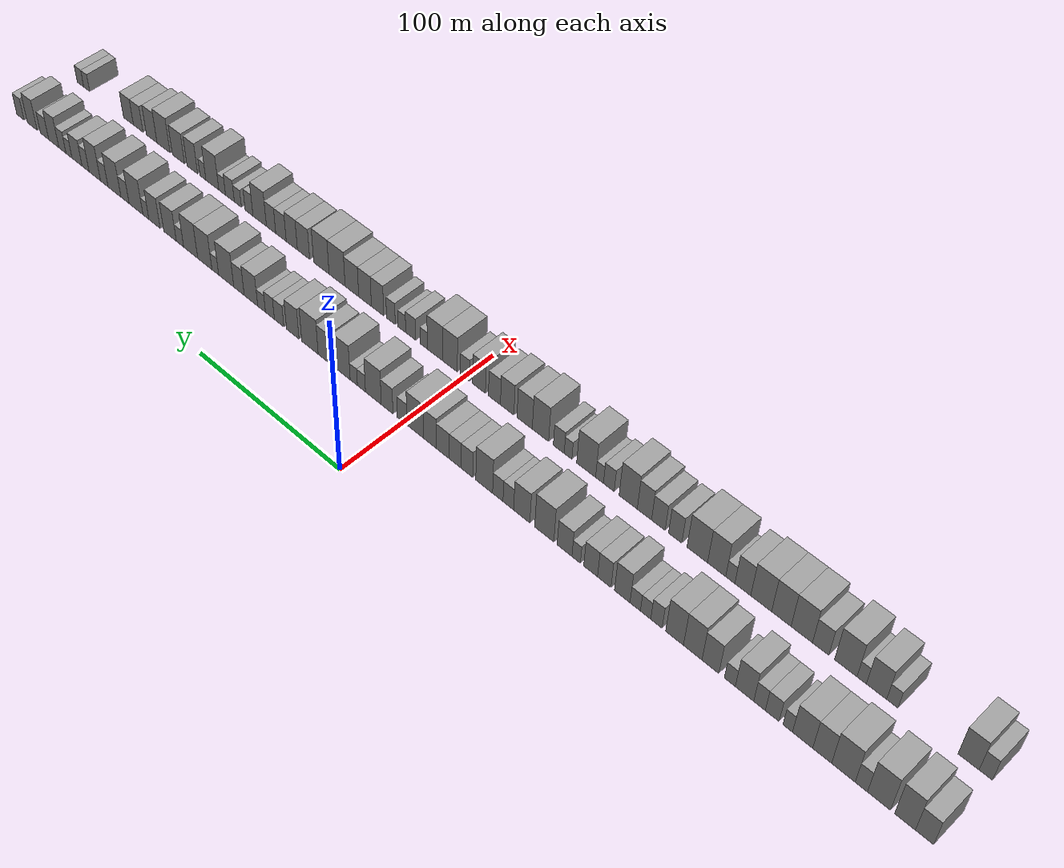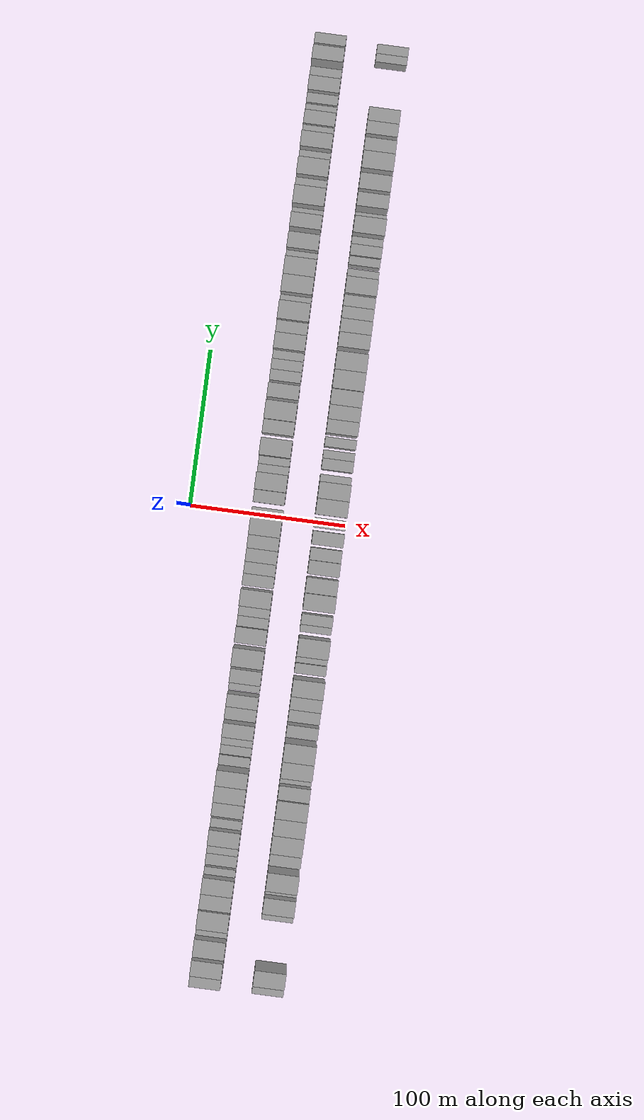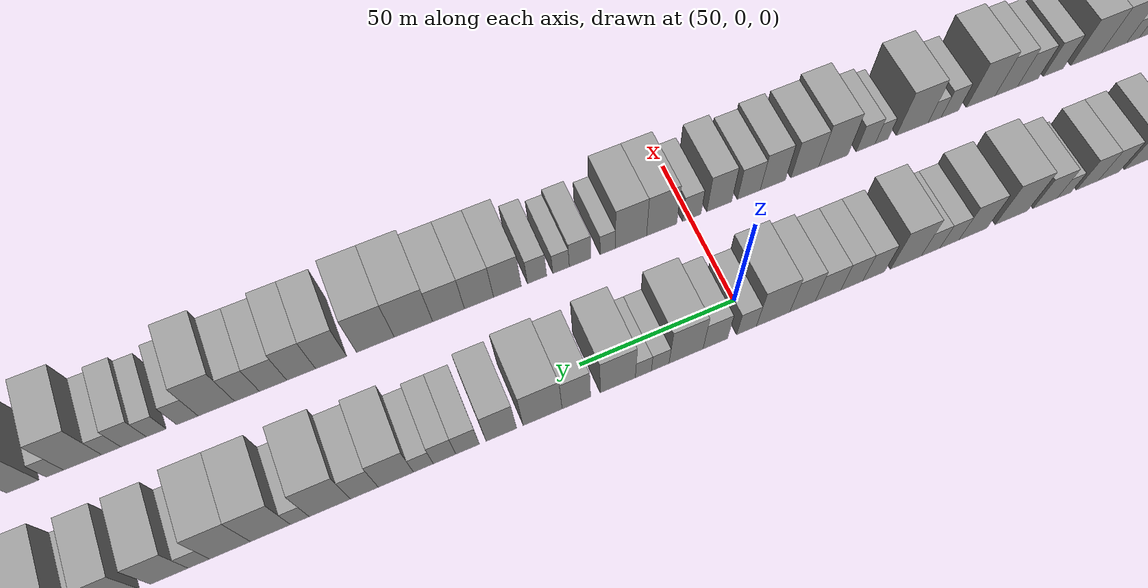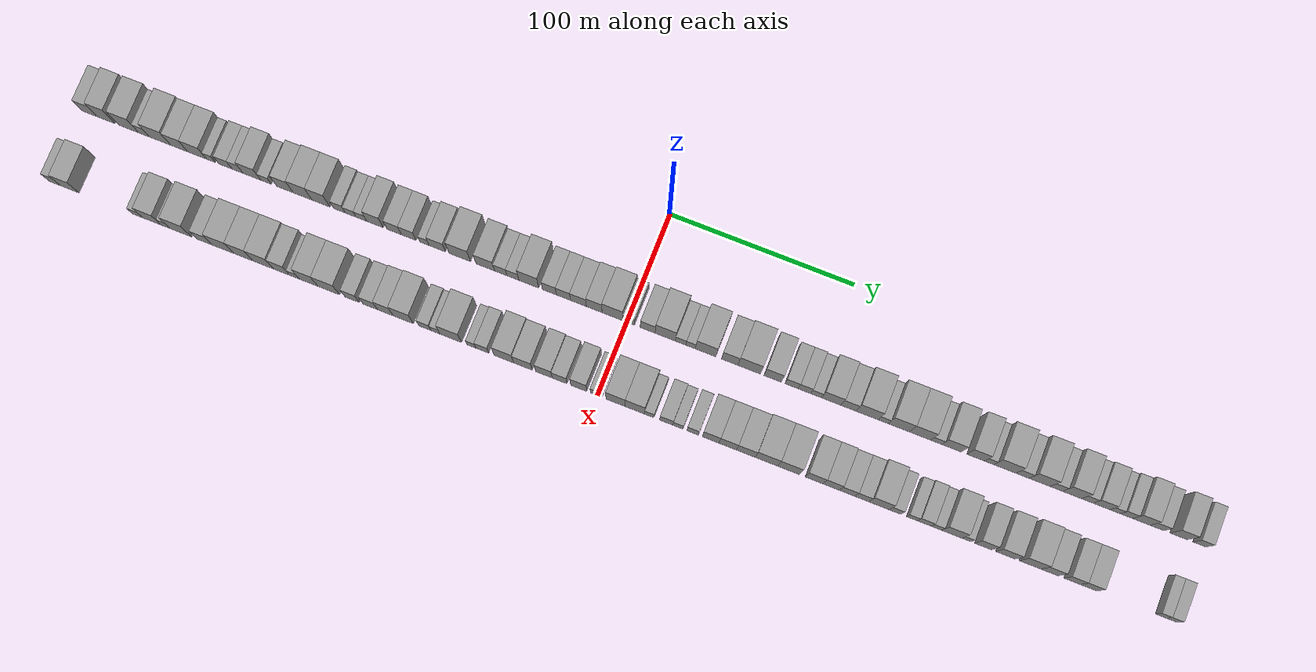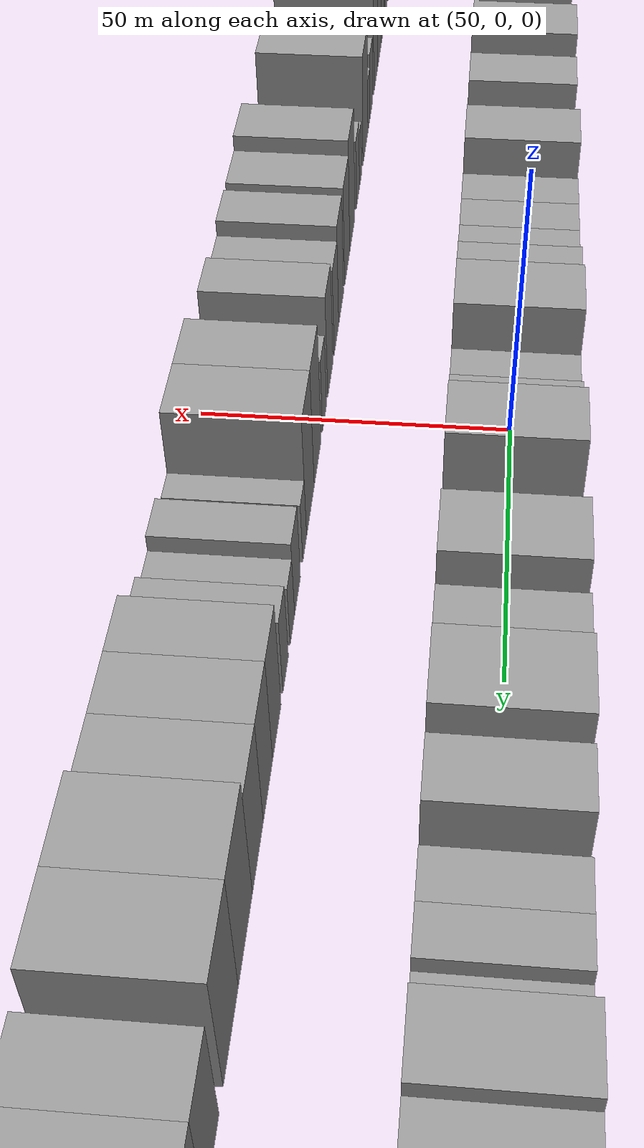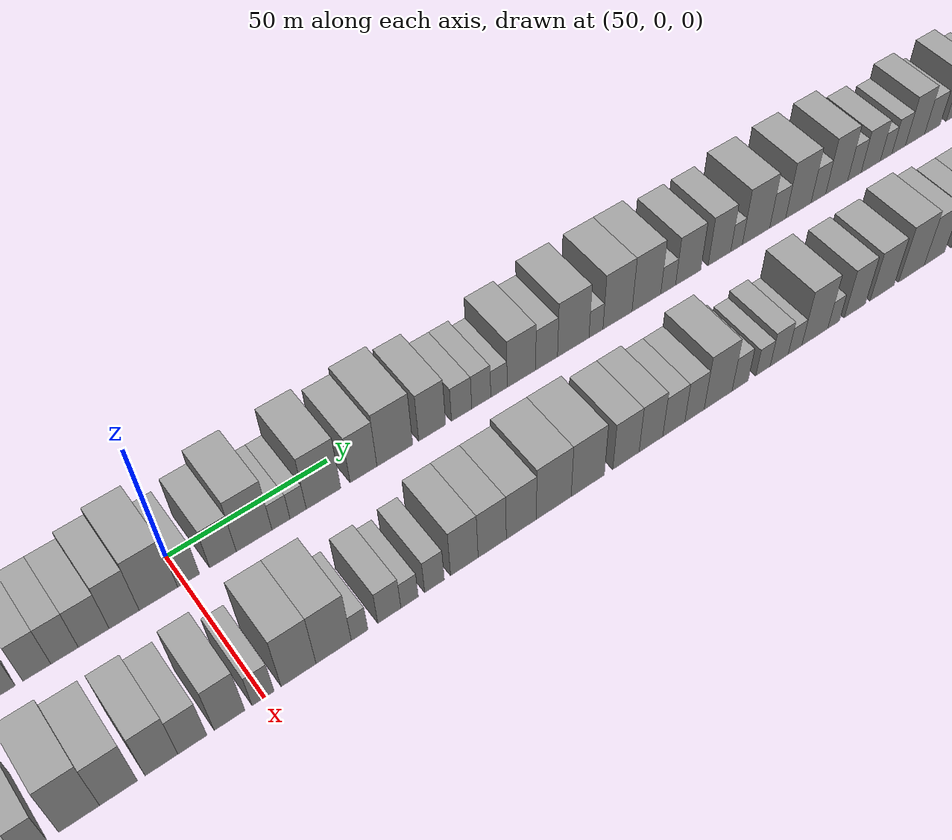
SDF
<sdf version="1.6">
 <world name="default">
  <scene>
   <sky><clouds><speed>12</speed></clouds></sky>
   <ambient>0.4 0.4 0.4 1</ambient>
   <background>0.7 0.7 0.7 1</background>
   <shadows>1</shadows>
  </scene>
  <gravity>0 0 -9.8066</gravity>
  <magnetic_field>6e-06 2.3e-05 -4.2e-05</magnetic_field>
  <physics default="0" name="default_physics" type="ode">
   <ode>
    <solver>
     <type>quick</type>
     <iters>10</iters>
     <sor>1.0</sor>
     <use_dynamic_moi_rescaling>0</use_dynamic_moi_rescaling>
    </solver>
    <constraints>
     <cfm>0</cfm>
     <erp>0.2</erp>
     <contact_max_correcting_vel>100</contact_max_correcting_vel>
     <contact_surface_layer>0.001</contact_surface_layer>
    </constraints>
   </ode>
   <max_step_size>0.004</max_step_size>
   <real_time_factor>1</real_time_factor>
   <real_time_update_rate>250</real_time_update_rate>
  </physics>
  <light name="sun" type="directional">
   <pose>0 0 10 0 0 0</pose>
   <diffuse>0.8 0.8 0.8 1</diffuse>
   <specular>0.2 0.2 0.2 1</specular>
   <attenuation>
    <range>1000</range>
    <constant>0.9</constant>
    <linear>0.01</linear>
    <quadratic>0.001</quadratic>
   </attenuation>
   <direction>-0.5 0.1 -0.9</direction>
  </light>
  <model name="building_1">
   <static>1</static>
   <pose>50.0000 -295.6604 0 0.000000 0.000000 0.000000</pose>
   <link name="link">
    <pose>0 0 9.00 0 0 0</pose>
    <collision name="collision"><geometry><box><size>20.0000 8.6792 18.0000</size></box></geometry></collision>
    <visual name="visual">
     <cast_shadows>0</cast_shadows>
     <geometry><box><size>20.0000 8.6792 18.0000</size></box></geometry>
     <material>
      <script>
       <uri>model://grey_wall/materials/scripts</uri>
       <uri>model://grey_wall/materials/textures</uri>
       <name>vrc/grey_wall</name>
      </script>
     </material>
    </visual>
   </link>
  </model>
  <model name="building_2">
   <static>1</static>
   <pose>50.0000 -286.3089 0 0.000000 0.000000 0.000000</pose>
   <link name="link">
    <pose>0 0 12.00 0 0 0</pose>
    <collision name="collision"><geometry><box><size>20.0000 10.0237 24.0000</size></box></geometry></collision>
    <visual name="visual">
     <cast_shadows>0</cast_shadows>
     <geometry><box><size>20.0000 10.0237 24.0000</size></box></geometry>
     <material>
      <script>
       <uri>model://grey_wall/materials/scripts</uri>
       <uri>model://grey_wall/materials/textures</uri>
       <name>vrc/grey_wall</name>
      </script>
     </material>
    </visual>
   </link>
  </model>
  <model name="building_3">
   <static>1</static>
   <pose>50.0000 -273.6609 0 0.000000 0.000000 0.000000</pose>
   <link name="link">
    <pose>0 0 12.00 0 0 0</pose>
    <collision name="collision"><geometry><box><size>20.0000 11.2724 24.0000</size></box></geometry></collision>
    <visual name="visual">
     <cast_shadows>0</cast_shadows>
     <geometry><box><size>20.0000 11.2724 24.0000</size></box></geometry>
     <material>
      <script>
       <uri>model://grey_wall/materials/scripts</uri>
       <uri>model://grey_wall/materials/textures</uri>
       <name>vrc/grey_wall</name>
      </script>
     </material>
    </visual>
   </link>
  </model>
  <model name="building_4">
   <static>1</static>
   <pose>50.0000 -264.9814 0 0.000000 0.000000 0.000000</pose>
   <link name="link">
    <pose>0 0 7.50 0 0 0</pose>
    <collision name="collision"><geometry><box><size>20.0000 6.0866 15.0000</size></box></geometry></collision>
    <visual name="visual">
     <cast_shadows>0</cast_shadows>
     <geometry><box><size>20.0000 6.0866 15.0000</size></box></geometry>
     <material>
      <script>
       <uri>model://grey_wall/materials/scripts</uri>
       <uri>model://grey_wall/materials/textures</uri>
       <name>vrc/grey_wall</name>
      </script>
     </material>
    </visual>
   </link>
  </model>
  <model name="building_5">
   <static>1</static>
   <pose>50.0000 -256.0350 0 0.000000 0.000000 0.000000</pose>
   <link name="link">
    <pose>0 0 12.00 0 0 0</pose>
    <collision name="collision"><geometry><box><size>20.0000 11.8062 24.0000</size></box></geometry></collision>
    <visual name="visual">
     <cast_shadows>0</cast_shadows>
     <geometry><box><size>20.0000 11.8062 24.0000</size></box></geometry>
     <material>
      <script>
       <uri>model://grey_wall/materials/scripts</uri>
       <uri>model://grey_wall/materials/textures</uri>
       <name>vrc/grey_wall</name>
      </script>
     </material>
    </visual>
   </link>
  </model>
  <model name="building_6">
   <static>1</static>
   <pose>50.0000 -245.3482 0 0.000000 0.000000 0.000000</pose>
   <link name="link">
    <pose>0 0 10.50 0 0 0</pose>
    <collision name="collision"><geometry><box><size>20.0000 9.5675 21.0000</size></box></geometry></collision>
    <visual name="visual">
     <cast_shadows>0</cast_shadows>
     <geometry><box><size>20.0000 9.5675 21.0000</size></box></geometry>
     <material>
      <script>
       <uri>model://grey_wall/materials/scripts</uri>
       <uri>model://grey_wall/materials/textures</uri>
       <name>vrc/grey_wall</name>
      </script>
     </material>
    </visual>
   </link>
  </model>
  <model name="building_7">
   <static>1</static>
   <pose>50.0000 -235.3438 0 0.000000 0.000000 0.000000</pose>
   <link name="link">
    <pose>0 0 10.50 0 0 0</pose>
    <collision name="collision"><geometry><box><size>20.0000 10.4414 21.0000</size></box></geometry></collision>
    <visual name="visual">
     <cast_shadows>0</cast_shadows>
     <geometry><box><size>20.0000 10.4414 21.0000</size></box></geometry>
     <material>
      <script>
       <uri>model://grey_wall/materials/scripts</uri>
       <uri>model://grey_wall/materials/textures</uri>
       <name>vrc/grey_wall</name>
      </script>
     </material>
    </visual>
   </link>
  </model>
  <model name="building_8">
   <static>1</static>
   <pose>50.0000 -227.6628 0 0.000000 0.000000 0.000000</pose>
   <link name="link">
    <pose>0 0 6.00 0 0 0</pose>
    <collision name="collision"><geometry><box><size>20.0000 4.9206 12.0000</size></box></geometry></collision>
    <visual name="visual">
     <cast_shadows>0</cast_shadows>
     <geometry><box><size>20.0000 4.9206 12.0000</size></box></geometry>
     <material>
      <script>
       <uri>model://grey_wall/materials/scripts</uri>
       <uri>model://grey_wall/materials/textures</uri>
       <name>vrc/grey_wall</name>
      </script>
     </material>
    </visual>
   </link>
  </model>
  <model name="building_9">
   <static>1</static>
   <pose>50.0000 -219.5754 0 0.000000 0.000000 0.000000</pose>
   <link name="link">
    <pose>0 0 7.50 0 0 0</pose>
    <collision name="collision"><geometry><box><size>20.0000 7.2541 15.0000</size></box></geometry></collision>
    <visual name="visual">
     <cast_shadows>0</cast_shadows>
     <geometry><box><size>20.0000 7.2541 15.0000</size></box></geometry>
     <material>
      <script>
       <uri>model://grey_wall/materials/scripts</uri>
       <uri>model://grey_wall/materials/textures</uri>
       <name>vrc/grey_wall</name>
      </script>
     </material>
    </visual>
   </link>
  </model>
  <model name="building_10">
   <static>1</static>
   <pose>50.0000 -212.8982 0 0.000000 0.000000 0.000000</pose>
   <link name="link">
    <pose>0 0 7.50 0 0 0</pose>
    <collision name="collision"><geometry><box><size>20.0000 6.1003 15.0000</size></box></geometry></collision>
    <visual name="visual">
     <cast_shadows>0</cast_shadows>
     <geometry><box><size>20.0000 6.1003 15.0000</size></box></geometry>
     <material>
      <script>
       <uri>model://grey_wall/materials/scripts</uri>
       <uri>model://grey_wall/materials/textures</uri>
       <name>vrc/grey_wall</name>
      </script>
     </material>
    </visual>
   </link>
  </model>
  <model name="building_11">
   <static>1</static>
   <pose>50.0000 -204.9200 0 0.000000 0.000000 0.000000</pose>
   <link name="link">
    <pose>0 0 10.50 0 0 0</pose>
    <collision name="collision"><geometry><box><size>20.0000 9.8560 21.0000</size></box></geometry></collision>
    <visual name="visual">
     <cast_shadows>0</cast_shadows>
     <geometry><box><size>20.0000 9.8560 21.0000</size></box></geometry>
     <material>
      <script>
       <uri>model://grey_wall/materials/scripts</uri>
       <uri>model://grey_wall/materials/textures</uri>
       <name>vrc/grey_wall</name>
      </script>
     </material>
    </visual>
   </link>
  </model>
  <model name="building_12">
   <static>1</static>
   <pose>50.0000 -197.0589 0 0.000000 0.000000 0.000000</pose>
   <link name="link">
    <pose>0 0 6.00 0 0 0</pose>
    <collision name="collision"><geometry><box><size>20.0000 5.8663 12.0000</size></box></geometry></collision>
    <visual name="visual">
     <cast_shadows>0</cast_shadows>
     <geometry><box><size>20.0000 5.8663 12.0000</size></box></geometry>
     <material>
      <script>
       <uri>model://grey_wall/materials/scripts</uri>
       <uri>model://grey_wall/materials/textures</uri>
       <name>vrc/grey_wall</name>
      </script>
     </material>
    </visual>
   </link>
  </model>
  <model name="building_13">
   <static>1</static>
   <pose>50.0000 -186.5327 0 0.000000 0.000000 0.000000</pose>
   <link name="link">
    <pose>0 0 10.50 0 0 0</pose>
    <collision name="collision"><geometry><box><size>20.0000 9.1861 21.0000</size></box></geometry></collision>
    <visual name="visual">
     <cast_shadows>0</cast_shadows>
     <geometry><box><size>20.0000 9.1861 21.0000</size></box></geometry>
     <material>
      <script>
       <uri>model://grey_wall/materials/scripts</uri>
       <uri>model://grey_wall/materials/textures</uri>
       <name>vrc/grey_wall</name>
      </script>
     </material>
    </visual>
   </link>
  </model>
  <model name="building_14">
   <static>1</static>
   <pose>50.0000 -176.8102 0 0.000000 0.000000 0.000000</pose>
   <link name="link">
    <pose>0 0 12.00 0 0 0</pose>
    <collision name="collision"><geometry><box><size>20.0000 10.2588 24.0000</size></box></geometry></collision>
    <visual name="visual">
     <cast_shadows>0</cast_shadows>
     <geometry><box><size>20.0000 10.2588 24.0000</size></box></geometry>
     <material>
      <script>
       <uri>model://grey_wall/materials/scripts</uri>
       <uri>model://grey_wall/materials/textures</uri>
       <name>vrc/grey_wall</name>
      </script>
     </material>
    </visual>
   </link>
  </model>
  <model name="building_15">
   <static>1</static>
   <pose>50.0000 -166.6893 0 0.000000 0.000000 0.000000</pose>
   <link name="link">
    <pose>0 0 12.00 0 0 0</pose>
    <collision name="collision"><geometry><box><size>20.0000 9.9830 24.0000</size></box></geometry></collision>
    <visual name="visual">
     <cast_shadows>0</cast_shadows>
     <geometry><box><size>20.0000 9.9830 24.0000</size></box></geometry>
     <material>
      <script>
       <uri>model://grey_wall/materials/scripts</uri>
       <uri>model://grey_wall/materials/textures</uri>
       <name>vrc/grey_wall</name>
      </script>
     </material>
    </visual>
   </link>
  </model>
  <model name="building_16">
   <static>1</static>
   <pose>50.0000 -156.4822 0 0.000000 0.000000 0.000000</pose>
   <link name="link">
    <pose>0 0 7.50 0 0 0</pose>
    <collision name="collision"><geometry><box><size>20.0000 6.4312 15.0000</size></box></geometry></collision>
    <visual name="visual">
     <cast_shadows>0</cast_shadows>
     <geometry><box><size>20.0000 6.4312 15.0000</size></box></geometry>
     <material>
      <script>
       <uri>model://grey_wall/materials/scripts</uri>
       <uri>model://grey_wall/materials/textures</uri>
       <name>vrc/grey_wall</name>
      </script>
     </material>
    </visual>
   </link>
  </model>
  <model name="building_17">
   <static>1</static>
   <pose>50.0000 -150.3267 0 0.000000 0.000000 0.000000</pose>
   <link name="link">
    <pose>0 0 6.00 0 0 0</pose>
    <collision name="collision"><geometry><box><size>20.0000 5.8798 12.0000</size></box></geometry></collision>
    <visual name="visual">
     <cast_shadows>0</cast_shadows>
     <geometry><box><size>20.0000 5.8798 12.0000</size></box></geometry>
     <material>
      <script>
       <uri>model://grey_wall/materials/scripts</uri>
       <uri>model://grey_wall/materials/textures</uri>
       <name>vrc/grey_wall</name>
      </script>
     </material>
    </visual>
   </link>
  </model>
  <model name="building_18">
   <static>1</static>
   <pose>50.0000 -144.3886 0 0.000000 0.000000 0.000000</pose>
   <link name="link">
    <pose>0 0 6.00 0 0 0</pose>
    <collision name="collision"><geometry><box><size>20.0000 5.9963 12.0000</size></box></geometry></collision>
    <visual name="visual">
     <cast_shadows>0</cast_shadows>
     <geometry><box><size>20.0000 5.9963 12.0000</size></box></geometry>
     <material>
      <script>
       <uri>model://grey_wall/materials/scripts</uri>
       <uri>model://grey_wall/materials/textures</uri>
       <name>vrc/grey_wall</name>
      </script>
     </material>
    </visual>
   </link>
  </model>
  <model name="building_19">
   <static>1</static>
   <pose>50.0000 -136.8716 0 0.000000 0.000000 0.000000</pose>
   <link name="link">
    <pose>0 0 10.50 0 0 0</pose>
    <collision name="collision"><geometry><box><size>20.0000 9.0378 21.0000</size></box></geometry></collision>
    <visual name="visual">
     <cast_shadows>0</cast_shadows>
     <geometry><box><size>20.0000 9.0378 21.0000</size></box></geometry>
     <material>
      <script>
       <uri>model://grey_wall/materials/scripts</uri>
       <uri>model://grey_wall/materials/textures</uri>
       <name>vrc/grey_wall</name>
      </script>
     </material>
    </visual>
   </link>
  </model>
  <model name="building_20">
   <static>1</static>
   <pose>50.0000 -126.3946 0 0.000000 0.000000 0.000000</pose>
   <link name="link">
    <pose>0 0 9.00 0 0 0</pose>
    <collision name="collision"><geometry><box><size>20.0000 7.9164 18.0000</size></box></geometry></collision>
    <visual name="visual">
     <cast_shadows>0</cast_shadows>
     <geometry><box><size>20.0000 7.9164 18.0000</size></box></geometry>
     <material>
      <script>
       <uri>model://grey_wall/materials/scripts</uri>
       <uri>model://grey_wall/materials/textures</uri>
       <name>vrc/grey_wall</name>
      </script>
     </material>
    </visual>
   </link>
  </model>
  <model name="building_21">
   <static>1</static>
   <pose>50.0000 -118.3697 0 0.000000 0.000000 0.000000</pose>
   <link name="link">
    <pose>0 0 9.00 0 0 0</pose>
    <collision name="collision"><geometry><box><size>20.0000 8.1333 18.0000</size></box></geometry></collision>
    <visual name="visual">
     <cast_shadows>0</cast_shadows>
     <geometry><box><size>20.0000 8.1333 18.0000</size></box></geometry>
     <material>
      <script>
       <uri>model://grey_wall/materials/scripts</uri>
       <uri>model://grey_wall/materials/textures</uri>
       <name>vrc/grey_wall</name>
      </script>
     </material>
    </visual>
   </link>
  </model>
  <model name="building_22">
   <static>1</static>
   <pose>50.0000 -109.7680 0 0.000000 0.000000 0.000000</pose>
   <link name="link">
    <pose>0 0 6.00 0 0 0</pose>
    <collision name="collision"><geometry><box><size>20.0000 5.0701 12.0000</size></box></geometry></collision>
    <visual name="visual">
     <cast_shadows>0</cast_shadows>
     <geometry><box><size>20.0000 5.0701 12.0000</size></box></geometry>
     <material>
      <script>
       <uri>model://grey_wall/materials/scripts</uri>
       <uri>model://grey_wall/materials/textures</uri>
       <name>vrc/grey_wall</name>
      </script>
     </material>
    </visual>
   </link>
  </model>
  <model name="building_23">
   <static>1</static>
   <pose>50.0000 -102.7718 0 0.000000 0.000000 0.000000</pose>
   <link name="link">
    <pose>0 0 9.00 0 0 0</pose>
    <collision name="collision"><geometry><box><size>20.0000 8.9224 18.0000</size></box></geometry></collision>
    <visual name="visual">
     <cast_shadows>0</cast_shadows>
     <geometry><box><size>20.0000 8.9224 18.0000</size></box></geometry>
     <material>
      <script>
       <uri>model://grey_wall/materials/scripts</uri>
       <uri>model://grey_wall/materials/textures</uri>
       <name>vrc/grey_wall</name>
      </script>
     </material>
    </visual>
   </link>
  </model>
  <model name="building_24">
   <static>1</static>
   <pose>50.0000 -90.4507 0 0.000000 0.000000 0.000000</pose>
   <link name="link">
    <pose>0 0 12.00 0 0 0</pose>
    <collision name="collision"><geometry><box><size>20.0000 11.7199 24.0000</size></box></geometry></collision>
    <visual name="visual">
     <cast_shadows>0</cast_shadows>
     <geometry><box><size>20.0000 11.7199 24.0000</size></box></geometry>
     <material>
      <script>
       <uri>model://grey_wall/materials/scripts</uri>
       <uri>model://grey_wall/materials/textures</uri>
       <name>vrc/grey_wall</name>
      </script>
     </material>
    </visual>
   </link>
  </model>
  <model name="building_25">
   <static>1</static>
   <pose>50.0000 -76.5439 0 0.000000 0.000000 0.000000</pose>
   <link name="link">
    <pose>0 0 10.50 0 0 0</pose>
    <collision name="collision"><geometry><box><size>20.0000 10.0936 21.0000</size></box></geometry></collision>
    <visual name="visual">
     <cast_shadows>0</cast_shadows>
     <geometry><box><size>20.0000 10.0936 21.0000</size></box></geometry>
     <material>
      <script>
       <uri>model://grey_wall/materials/scripts</uri>
       <uri>model://grey_wall/materials/textures</uri>
       <name>vrc/grey_wall</name>
      </script>
     </material>
    </visual>
   </link>
  </model>
  <model name="building_26">
   <static>1</static>
   <pose>50.0000 -68.1587 0 0.000000 0.000000 0.000000</pose>
   <link name="link">
    <pose>0 0 7.50 0 0 0</pose>
    <collision name="collision"><geometry><box><size>20.0000 6.6767 15.0000</size></box></geometry></collision>
    <visual name="visual">
     <cast_shadows>0</cast_shadows>
     <geometry><box><size>20.0000 6.6767 15.0000</size></box></geometry>
     <material>
      <script>
       <uri>model://grey_wall/materials/scripts</uri>
       <uri>model://grey_wall/materials/textures</uri>
       <name>vrc/grey_wall</name>
      </script>
     </material>
    </visual>
   </link>
  </model>
  <model name="building_27">
   <static>1</static>
   <pose>50.0000 -61.5330 0 0.000000 0.000000 0.000000</pose>
   <link name="link">
    <pose>0 0 7.50 0 0 0</pose>
    <collision name="collision"><geometry><box><size>20.0000 6.5746 15.0000</size></box></geometry></collision>
    <visual name="visual">
     <cast_shadows>0</cast_shadows>
     <geometry><box><size>20.0000 6.5746 15.0000</size></box></geometry>
     <material>
      <script>
       <uri>model://grey_wall/materials/scripts</uri>
       <uri>model://grey_wall/materials/textures</uri>
       <name>vrc/grey_wall</name>
      </script>
     </material>
    </visual>
   </link>
  </model>
  <model name="building_28">
   <static>1</static>
   <pose>50.0000 -52.8710 0 0.000000 0.000000 0.000000</pose>
   <link name="link">
    <pose>0 0 12.00 0 0 0</pose>
    <collision name="collision"><geometry><box><size>20.0000 10.7494 24.0000</size></box></geometry></collision>
    <visual name="visual">
     <cast_shadows>0</cast_shadows>
     <geometry><box><size>20.0000 10.7494 24.0000</size></box></geometry>
     <material>
      <script>
       <uri>model://grey_wall/materials/scripts</uri>
       <uri>model://grey_wall/materials/textures</uri>
       <name>vrc/grey_wall</name>
      </script>
     </material>
    </visual>
   </link>
  </model>
  <model name="building_29">
   <static>1</static>
   <pose>50.0000 -41.6983 0 0.000000 0.000000 0.000000</pose>
   <link name="link">
    <pose>0 0 9.00 0 0 0</pose>
    <collision name="collision"><geometry><box><size>20.0000 7.5961 18.0000</size></box></geometry></collision>
    <visual name="visual">
     <cast_shadows>0</cast_shadows>
     <geometry><box><size>20.0000 7.5961 18.0000</size></box></geometry>
     <material>
      <script>
       <uri>model://grey_wall/materials/scripts</uri>
       <uri>model://grey_wall/materials/textures</uri>
       <name>vrc/grey_wall</name>
      </script>
     </material>
    </visual>
   </link>
  </model>
  <model name="building_30">
   <static>1</static>
   <pose>50.0000 -34.1289 0 0.000000 0.000000 0.000000</pose>
   <link name="link">
    <pose>0 0 9.00 0 0 0</pose>
    <collision name="collision"><geometry><box><size>20.0000 7.5425 18.0000</size></box></geometry></collision>
    <visual name="visual">
     <cast_shadows>0</cast_shadows>
     <geometry><box><size>20.0000 7.5425 18.0000</size></box></geometry>
     <material>
      <script>
       <uri>model://grey_wall/materials/scripts</uri>
       <uri>model://grey_wall/materials/textures</uri>
       <name>vrc/grey_wall</name>
      </script>
     </material>
    </visual>
   </link>
  </model>
  <model name="building_31">
   <static>1</static>
   <pose>50.0000 -26.0431 0 0.000000 0.000000 0.000000</pose>
   <link name="link">
    <pose>0 0 9.00 0 0 0</pose>
    <collision name="collision"><geometry><box><size>20.0000 8.6293 18.0000</size></box></geometry></collision>
    <visual name="visual">
     <cast_shadows>0</cast_shadows>
     <geometry><box><size>20.0000 8.6293 18.0000</size></box></geometry>
     <material>
      <script>
       <uri>model://grey_wall/materials/scripts</uri>
       <uri>model://grey_wall/materials/textures</uri>
       <name>vrc/grey_wall</name>
      </script>
     </material>
    </visual>
   </link>
  </model>
  <model name="building_32">
   <static>1</static>
   <pose>50.0000 -17.4651 0 0.000000 0.000000 0.000000</pose>
   <link name="link">
    <pose>0 0 10.50 0 0 0</pose>
    <collision name="collision"><geometry><box><size>20.0000 8.5266 21.0000</size></box></geometry></collision>
    <visual name="visual">
     <cast_shadows>0</cast_shadows>
     <geometry><box><size>20.0000 8.5266 21.0000</size></box></geometry>
     <material>
      <script>
       <uri>model://grey_wall/materials/scripts</uri>
       <uri>model://grey_wall/materials/textures</uri>
       <name>vrc/grey_wall</name>
      </script>
     </material>
    </visual>
   </link>
  </model>
  <model name="building_33">
   <static>1</static>
   <pose>50.0000 -7.6380 0 0.000000 0.000000 0.000000</pose>
   <link name="link">
    <pose>0 0 12.00 0 0 0</pose>
    <collision name="collision"><geometry><box><size>20.0000 11.1276 24.0000</size></box></geometry></collision>
    <visual name="visual">
     <cast_shadows>0</cast_shadows>
     <geometry><box><size>20.0000 11.1276 24.0000</size></box></geometry>
     <material>
      <script>
       <uri>model://grey_wall/materials/scripts</uri>
       <uri>model://grey_wall/materials/textures</uri>
       <name>vrc/grey_wall</name>
      </script>
     </material>
    </visual>
   </link>
  </model>
  <model name="building_34">
   <static>1</static>
   <pose>50.0000 1.1589 0 0.000000 0.000000 0.000000</pose>
   <link name="link">
    <pose>0 0 7.50 0 0 0</pose>
    <collision name="collision"><geometry><box><size>20.0000 6.4662 15.0000</size></box></geometry></collision>
    <visual name="visual">
     <cast_shadows>0</cast_shadows>
     <geometry><box><size>20.0000 6.4662 15.0000</size></box></geometry>
     <material>
      <script>
       <uri>model://grey_wall/materials/scripts</uri>
       <uri>model://grey_wall/materials/textures</uri>
       <name>vrc/grey_wall</name>
      </script>
     </material>
    </visual>
   </link>
  </model>
  <model name="building_35">
   <static>1</static>
   <pose>50.0000 11.3959 0 0.000000 0.000000 0.000000</pose>
   <link name="link">
    <pose>0 0 9.00 0 0 0</pose>
    <collision name="collision"><geometry><box><size>20.0000 8.0078 18.0000</size></box></geometry></collision>
    <visual name="visual">
     <cast_shadows>0</cast_shadows>
     <geometry><box><size>20.0000 8.0078 18.0000</size></box></geometry>
     <material>
      <script>
       <uri>model://grey_wall/materials/scripts</uri>
       <uri>model://grey_wall/materials/textures</uri>
       <name>vrc/grey_wall</name>
      </script>
     </material>
    </visual>
   </link>
  </model>
  <model name="building_36">
   <static>1</static>
   <pose>50.0000 20.8704 0 0.000000 0.000000 0.000000</pose>
   <link name="link">
    <pose>0 0 12.00 0 0 0</pose>
    <collision name="collision"><geometry><box><size>20.0000 10.9411 24.0000</size></box></geometry></collision>
    <visual name="visual">
     <cast_shadows>0</cast_shadows>
     <geometry><box><size>20.0000 10.9411 24.0000</size></box></geometry>
     <material>
      <script>
       <uri>model://grey_wall/materials/scripts</uri>
       <uri>model://grey_wall/materials/textures</uri>
       <name>vrc/grey_wall</name>
      </script>
     </material>
    </visual>
   </link>
  </model>
  <model name="building_37">
   <static>1</static>
   <pose>50.0000 29.1648 0 0.000000 0.000000 0.000000</pose>
   <link name="link">
    <pose>0 0 6.00 0 0 0</pose>
    <collision name="collision"><geometry><box><size>20.0000 5.6477 12.0000</size></box></geometry></collision>
    <visual name="visual">
     <cast_shadows>0</cast_shadows>
     <geometry><box><size>20.0000 5.6477 12.0000</size></box></geometry>
     <material>
      <script>
       <uri>model://grey_wall/materials/scripts</uri>
       <uri>model://grey_wall/materials/textures</uri>
       <name>vrc/grey_wall</name>
      </script>
     </material>
    </visual>
   </link>
  </model>
  <model name="building_38">
   <static>1</static>
   <pose>50.0000 34.5339 0 0.000000 0.000000 0.000000</pose>
   <link name="link">
    <pose>0 0 6.00 0 0 0</pose>
    <collision name="collision"><geometry><box><size>20.0000 5.0903 12.0000</size></box></geometry></collision>
    <visual name="visual">
     <cast_shadows>0</cast_shadows>
     <geometry><box><size>20.0000 5.0903 12.0000</size></box></geometry>
     <material>
      <script>
       <uri>model://grey_wall/materials/scripts</uri>
       <uri>model://grey_wall/materials/textures</uri>
       <name>vrc/grey_wall</name>
      </script>
     </material>
    </visual>
   </link>
  </model>
  <model name="building_39">
   <static>1</static>
   <pose>50.0000 42.5966 0 0.000000 0.000000 0.000000</pose>
   <link name="link">
    <pose>0 0 12.00 0 0 0</pose>
    <collision name="collision"><geometry><box><size>20.0000 11.0351 24.0000</size></box></geometry></collision>
    <visual name="visual">
     <cast_shadows>0</cast_shadows>
     <geometry><box><size>20.0000 11.0351 24.0000</size></box></geometry>
     <material>
      <script>
       <uri>model://grey_wall/materials/scripts</uri>
       <uri>model://grey_wall/materials/textures</uri>
       <name>vrc/grey_wall</name>
      </script>
     </material>
    </visual>
   </link>
  </model>
  <model name="building_40">
   <static>1</static>
   <pose>50.0000 55.5203 0 0.000000 0.000000 0.000000</pose>
   <link name="link">
    <pose>0 0 10.50 0 0 0</pose>
    <collision name="collision"><geometry><box><size>20.0000 8.8122 21.0000</size></box></geometry></collision>
    <visual name="visual">
     <cast_shadows>0</cast_shadows>
     <geometry><box><size>20.0000 8.8122 21.0000</size></box></geometry>
     <material>
      <script>
       <uri>model://grey_wall/materials/scripts</uri>
       <uri>model://grey_wall/materials/textures</uri>
       <name>vrc/grey_wall</name>
      </script>
     </material>
    </visual>
   </link>
  </model>
  <model name="building_41">
   <static>1</static>
   <pose>50.0000 65.8986 0 0.000000 0.000000 0.000000</pose>
   <link name="link">
    <pose>0 0 12.00 0 0 0</pose>
    <collision name="collision"><geometry><box><size>20.0000 11.9445 24.0000</size></box></geometry></collision>
    <visual name="visual">
     <cast_shadows>0</cast_shadows>
     <geometry><box><size>20.0000 11.9445 24.0000</size></box></geometry>
     <material>
      <script>
       <uri>model://grey_wall/materials/scripts</uri>
       <uri>model://grey_wall/materials/textures</uri>
       <name>vrc/grey_wall</name>
      </script>
     </material>
    </visual>
   </link>
  </model>
  <model name="building_42">
   <static>1</static>
   <pose>50.0000 78.4836 0 0.000000 0.000000 0.000000</pose>
   <link name="link">
    <pose>0 0 10.50 0 0 0</pose>
    <collision name="collision"><geometry><box><size>20.0000 9.2255 21.0000</size></box></geometry></collision>
    <visual name="visual">
     <cast_shadows>0</cast_shadows>
     <geometry><box><size>20.0000 9.2255 21.0000</size></box></geometry>
     <material>
      <script>
       <uri>model://grey_wall/materials/scripts</uri>
       <uri>model://grey_wall/materials/textures</uri>
       <name>vrc/grey_wall</name>
      </script>
     </material>
    </visual>
   </link>
  </model>
  <model name="building_43">
   <static>1</static>
   <pose>50.0000 88.6178 0 0.000000 0.000000 0.000000</pose>
   <link name="link">
    <pose>0 0 7.50 0 0 0</pose>
    <collision name="collision"><geometry><box><size>20.0000 7.0429 15.0000</size></box></geometry></collision>
    <visual name="visual">
     <cast_shadows>0</cast_shadows>
     <geometry><box><size>20.0000 7.0429 15.0000</size></box></geometry>
     <material>
      <script>
       <uri>model://grey_wall/materials/scripts</uri>
       <uri>model://grey_wall/materials/textures</uri>
       <name>vrc/grey_wall</name>
      </script>
     </material>
    </visual>
   </link>
  </model>
  <model name="building_44">
   <static>1</static>
   <pose>50.0000 95.4951 0 0.000000 0.000000 0.000000</pose>
   <link name="link">
    <pose>0 0 7.50 0 0 0</pose>
    <collision name="collision"><geometry><box><size>20.0000 6.7116 15.0000</size></box></geometry></collision>
    <visual name="visual">
     <cast_shadows>0</cast_shadows>
     <geometry><box><size>20.0000 6.7116 15.0000</size></box></geometry>
     <material>
      <script>
       <uri>model://grey_wall/materials/scripts</uri>
       <uri>model://grey_wall/materials/textures</uri>
       <name>vrc/grey_wall</name>
      </script>
     </material>
    </visual>
   </link>
  </model>
  <model name="building_45">
   <static>1</static>
   <pose>50.0000 101.7632 0 0.000000 0.000000 0.000000</pose>
   <link name="link">
    <pose>0 0 6.00 0 0 0</pose>
    <collision name="collision"><geometry><box><size>20.0000 5.8247 12.0000</size></box></geometry></collision>
    <visual name="visual">
     <cast_shadows>0</cast_shadows>
     <geometry><box><size>20.0000 5.8247 12.0000</size></box></geometry>
     <material>
      <script>
       <uri>model://grey_wall/materials/scripts</uri>
       <uri>model://grey_wall/materials/textures</uri>
       <name>vrc/grey_wall</name>
      </script>
     </material>
    </visual>
   </link>
  </model>
  <model name="building_46">
   <static>1</static>
   <pose>50.0000 109.8124 0 0.000000 0.000000 0.000000</pose>
   <link name="link">
    <pose>0 0 10.50 0 0 0</pose>
    <collision name="collision"><geometry><box><size>20.0000 10.2737 21.0000</size></box></geometry></collision>
    <visual name="visual">
     <cast_shadows>0</cast_shadows>
     <geometry><box><size>20.0000 10.2737 21.0000</size></box></geometry>
     <material>
      <script>
       <uri>model://grey_wall/materials/scripts</uri>
       <uri>model://grey_wall/materials/textures</uri>
       <name>vrc/grey_wall</name>
      </script>
     </material>
    </visual>
   </link>
  </model>
  <model name="building_47">
   <static>1</static>
   <pose>50.0000 118.9649 0 0.000000 0.000000 0.000000</pose>
   <link name="link">
    <pose>0 0 9.00 0 0 0</pose>
    <collision name="collision"><geometry><box><size>20.0000 8.0313 18.0000</size></box></geometry></collision>
    <visual name="visual">
     <cast_shadows>0</cast_shadows>
     <geometry><box><size>20.0000 8.0313 18.0000</size></box></geometry>
     <material>
      <script>
       <uri>model://grey_wall/materials/scripts</uri>
       <uri>model://grey_wall/materials/textures</uri>
       <name>vrc/grey_wall</name>
      </script>
     </material>
    </visual>
   </link>
  </model>
  <model name="building_48">
   <static>1</static>
   <pose>50.0000 128.8710 0 0.000000 0.000000 0.000000</pose>
   <link name="link">
    <pose>0 0 12.00 0 0 0</pose>
    <collision name="collision"><geometry><box><size>20.0000 11.7810 24.0000</size></box></geometry></collision>
    <visual name="visual">
     <cast_shadows>0</cast_shadows>
     <geometry><box><size>20.0000 11.7810 24.0000</size></box></geometry>
     <material>
      <script>
       <uri>model://grey_wall/materials/scripts</uri>
       <uri>model://grey_wall/materials/textures</uri>
       <name>vrc/grey_wall</name>
      </script>
     </material>
    </visual>
   </link>
  </model>
  <model name="building_49">
   <static>1</static>
   <pose>50.0000 137.4100 0 0.000000 0.000000 0.000000</pose>
   <link name="link">
    <pose>0 0 6.00 0 0 0</pose>
    <collision name="collision"><geometry><box><size>20.0000 5.2969 12.0000</size></box></geometry></collision>
    <visual name="visual">
     <cast_shadows>0</cast_shadows>
     <geometry><box><size>20.0000 5.2969 12.0000</size></box></geometry>
     <material>
      <script>
       <uri>model://grey_wall/materials/scripts</uri>
       <uri>model://grey_wall/materials/textures</uri>
       <name>vrc/grey_wall</name>
      </script>
     </material>
    </visual>
   </link>
  </model>
  <model name="building_50">
   <static>1</static>
   <pose>50.0000 145.6631 0 0.000000 0.000000 0.000000</pose>
   <link name="link">
    <pose>0 0 12.00 0 0 0</pose>
    <collision name="collision"><geometry><box><size>20.0000 11.2093 24.0000</size></box></geometry></collision>
    <visual name="visual">
     <cast_shadows>0</cast_shadows>
     <geometry><box><size>20.0000 11.2093 24.0000</size></box></geometry>
     <material>
      <script>
       <uri>model://grey_wall/materials/scripts</uri>
       <uri>model://grey_wall/materials/textures</uri>
       <name>vrc/grey_wall</name>
      </script>
     </material>
    </visual>
   </link>
  </model>
  <model name="building_51">
   <static>1</static>
   <pose>50.0000 156.8992 0 0.000000 0.000000 0.000000</pose>
   <link name="link">
    <pose>0 0 12.00 0 0 0</pose>
    <collision name="collision"><geometry><box><size>20.0000 11.2628 24.0000</size></box></geometry></collision>
    <visual name="visual">
     <cast_shadows>0</cast_shadows>
     <geometry><box><size>20.0000 11.2628 24.0000</size></box></geometry>
     <material>
      <script>
       <uri>model://grey_wall/materials/scripts</uri>
       <uri>model://grey_wall/materials/textures</uri>
       <name>vrc/grey_wall</name>
      </script>
     </material>
    </visual>
   </link>
  </model>
  <model name="building_52">
   <static>1</static>
   <pose>50.0000 165.4799 0 0.000000 0.000000 0.000000</pose>
   <link name="link">
    <pose>0 0 6.00 0 0 0</pose>
    <collision name="collision"><geometry><box><size>20.0000 5.8987 12.0000</size></box></geometry></collision>
    <visual name="visual">
     <cast_shadows>0</cast_shadows>
     <geometry><box><size>20.0000 5.8987 12.0000</size></box></geometry>
     <material>
      <script>
       <uri>model://grey_wall/materials/scripts</uri>
       <uri>model://grey_wall/materials/textures</uri>
       <name>vrc/grey_wall</name>
      </script>
     </material>
    </visual>
   </link>
  </model>
  <model name="building_53">
   <static>1</static>
   <pose>50.0000 173.5300 0 0.000000 0.000000 0.000000</pose>
   <link name="link">
    <pose>0 0 10.50 0 0 0</pose>
    <collision name="collision"><geometry><box><size>20.0000 10.2016 21.0000</size></box></geometry></collision>
    <visual name="visual">
     <cast_shadows>0</cast_shadows>
     <geometry><box><size>20.0000 10.2016 21.0000</size></box></geometry>
     <material>
      <script>
       <uri>model://grey_wall/materials/scripts</uri>
       <uri>model://grey_wall/materials/textures</uri>
       <name>vrc/grey_wall</name>
      </script>
     </material>
    </visual>
   </link>
  </model>
  <model name="building_54">
   <static>1</static>
   <pose>50.0000 186.2834 0 0.000000 0.000000 0.000000</pose>
   <link name="link">
    <pose>0 0 10.50 0 0 0</pose>
    <collision name="collision"><geometry><box><size>20.0000 9.3051 21.0000</size></box></geometry></collision>
    <visual name="visual">
     <cast_shadows>0</cast_shadows>
     <geometry><box><size>20.0000 9.3051 21.0000</size></box></geometry>
     <material>
      <script>
       <uri>model://grey_wall/materials/scripts</uri>
       <uri>model://grey_wall/materials/textures</uri>
       <name>vrc/grey_wall</name>
      </script>
     </material>
    </visual>
   </link>
  </model>
  <model name="building_55">
   <static>1</static>
   <pose>50.0000 193.3706 0 0.000000 0.000000 0.000000</pose>
   <link name="link">
    <pose>0 0 6.00 0 0 0</pose>
    <collision name="collision"><geometry><box><size>20.0000 4.8694 12.0000</size></box></geometry></collision>
    <visual name="visual">
     <cast_shadows>0</cast_shadows>
     <geometry><box><size>20.0000 4.8694 12.0000</size></box></geometry>
     <material>
      <script>
       <uri>model://grey_wall/materials/scripts</uri>
       <uri>model://grey_wall/materials/textures</uri>
       <name>vrc/grey_wall</name>
      </script>
     </material>
    </visual>
   </link>
  </model>
  <model name="building_56">
   <static>1</static>
   <pose>50.0000 201.5925 0 0.000000 0.000000 0.000000</pose>
   <link name="link">
    <pose>0 0 12.00 0 0 0</pose>
    <collision name="collision"><geometry><box><size>20.0000 11.5745 24.0000</size></box></geometry></collision>
    <visual name="visual">
     <cast_shadows>0</cast_shadows>
     <geometry><box><size>20.0000 11.5745 24.0000</size></box></geometry>
     <material>
      <script>
       <uri>model://grey_wall/materials/scripts</uri>
       <uri>model://grey_wall/materials/textures</uri>
       <name>vrc/grey_wall</name>
      </script>
     </material>
    </visual>
   </link>
  </model>
  <model name="building_57">
   <static>1</static>
   <pose>50.0000 210.8056 0 0.000000 0.000000 0.000000</pose>
   <link name="link">
    <pose>0 0 7.50 0 0 0</pose>
    <collision name="collision"><geometry><box><size>20.0000 6.8518 15.0000</size></box></geometry></collision>
    <visual name="visual">
     <cast_shadows>0</cast_shadows>
     <geometry><box><size>20.0000 6.8518 15.0000</size></box></geometry>
     <material>
      <script>
       <uri>model://grey_wall/materials/scripts</uri>
       <uri>model://grey_wall/materials/textures</uri>
       <name>vrc/grey_wall</name>
      </script>
     </material>
    </visual>
   </link>
  </model>
  <model name="building_58">
   <static>1</static>
   <pose>50.0000 219.7498 0 0.000000 0.000000 0.000000</pose>
   <link name="link">
    <pose>0 0 12.00 0 0 0</pose>
    <collision name="collision"><geometry><box><size>20.0000 11.0365 24.0000</size></box></geometry></collision>
    <visual name="visual">
     <cast_shadows>0</cast_shadows>
     <geometry><box><size>20.0000 11.0365 24.0000</size></box></geometry>
     <material>
      <script>
       <uri>model://grey_wall/materials/scripts</uri>
       <uri>model://grey_wall/materials/textures</uri>
       <name>vrc/grey_wall</name>
      </script>
     </material>
    </visual>
   </link>
  </model>
  <model name="building_59">
   <static>1</static>
   <pose>50.0000 228.5095 0 0.000000 0.000000 0.000000</pose>
   <link name="link">
    <pose>0 0 7.50 0 0 0</pose>
    <collision name="collision"><geometry><box><size>20.0000 6.4829 15.0000</size></box></geometry></collision>
    <visual name="visual">
     <cast_shadows>0</cast_shadows>
     <geometry><box><size>20.0000 6.4829 15.0000</size></box></geometry>
     <material>
      <script>
       <uri>model://grey_wall/materials/scripts</uri>
       <uri>model://grey_wall/materials/textures</uri>
       <name>vrc/grey_wall</name>
      </script>
     </material>
    </visual>
   </link>
  </model>
  <model name="building_60">
   <static>1</static>
   <pose>50.0000 236.6931 0 0.000000 0.000000 0.000000</pose>
   <link name="link">
    <pose>0 0 12.00 0 0 0</pose>
    <collision name="collision"><geometry><box><size>20.0000 9.8843 24.0000</size></box></geometry></collision>
    <visual name="visual">
     <cast_shadows>0</cast_shadows>
     <geometry><box><size>20.0000 9.8843 24.0000</size></box></geometry>
     <material>
      <script>
       <uri>model://grey_wall/materials/scripts</uri>
       <uri>model://grey_wall/materials/textures</uri>
       <name>vrc/grey_wall</name>
      </script>
     </material>
    </visual>
   </link>
  </model>
  <model name="building_61">
   <static>1</static>
   <pose>50.0000 244.6765 0 0.000000 0.000000 0.000000</pose>
   <link name="link">
    <pose>0 0 7.50 0 0 0</pose>
    <collision name="collision"><geometry><box><size>20.0000 6.0823 15.0000</size></box></geometry></collision>
    <visual name="visual">
     <cast_shadows>0</cast_shadows>
     <geometry><box><size>20.0000 6.0823 15.0000</size></box></geometry>
     <material>
      <script>
       <uri>model://grey_wall/materials/scripts</uri>
       <uri>model://grey_wall/materials/textures</uri>
       <name>vrc/grey_wall</name>
      </script>
     </material>
    </visual>
   </link>
  </model>
  <model name="building_62">
   <static>1</static>
   <pose>50.0000 252.1347 0 0.000000 0.000000 0.000000</pose>
   <link name="link">
    <pose>0 0 9.00 0 0 0</pose>
    <collision name="collision"><geometry><box><size>20.0000 8.8340 18.0000</size></box></geometry></collision>
    <visual name="visual">
     <cast_shadows>0</cast_shadows>
     <geometry><box><size>20.0000 8.8340 18.0000</size></box></geometry>
     <material>
      <script>
       <uri>model://grey_wall/materials/scripts</uri>
       <uri>model://grey_wall/materials/textures</uri>
       <name>vrc/grey_wall</name>
      </script>
     </material>
    </visual>
   </link>
  </model>
  <model name="building_63">
   <static>1</static>
   <pose>50.0000 259.2328 0 0.000000 0.000000 0.000000</pose>
   <link name="link">
    <pose>0 0 6.00 0 0 0</pose>
    <collision name="collision"><geometry><box><size>20.0000 5.3622 12.0000</size></box></geometry></collision>
    <visual name="visual">
     <cast_shadows>0</cast_shadows>
     <geometry><box><size>20.0000 5.3622 12.0000</size></box></geometry>
     <material>
      <script>
       <uri>model://grey_wall/materials/scripts</uri>
       <uri>model://grey_wall/materials/textures</uri>
       <name>vrc/grey_wall</name>
      </script>
     </material>
    </visual>
   </link>
  </model>
  <model name="building_64">
   <static>1</static>
   <pose>50.0000 265.0786 0 0.000000 0.000000 0.000000</pose>
   <link name="link">
    <pose>0 0 7.50 0 0 0</pose>
    <collision name="collision"><geometry><box><size>20.0000 6.3295 15.0000</size></box></geometry></collision>
    <visual name="visual">
     <cast_shadows>0</cast_shadows>
     <geometry><box><size>20.0000 6.3295 15.0000</size></box></geometry>
     <material>
      <script>
       <uri>model://grey_wall/materials/scripts</uri>
       <uri>model://grey_wall/materials/textures</uri>
       <name>vrc/grey_wall</name>
      </script>
     </material>
    </visual>
   </link>
  </model>
  <model name="building_65">
   <static>1</static>
   <pose>50.0000 272.8066 0 0.000000 0.000000 0.000000</pose>
   <link name="link">
    <pose>0 0 10.50 0 0 0</pose>
    <collision name="collision"><geometry><box><size>20.0000 9.1265 21.0000</size></box></geometry></collision>
    <visual name="visual">
     <cast_shadows>0</cast_shadows>
     <geometry><box><size>20.0000 9.1265 21.0000</size></box></geometry>
     <material>
      <script>
       <uri>model://grey_wall/materials/scripts</uri>
       <uri>model://grey_wall/materials/textures</uri>
       <name>vrc/grey_wall</name>
      </script>
     </material>
    </visual>
   </link>
  </model>
  <model name="building_66">
   <static>1</static>
   <pose>50.0000 281.0966 0 0.000000 0.000000 0.000000</pose>
   <link name="link">
    <pose>0 0 7.50 0 0 0</pose>
    <collision name="collision"><geometry><box><size>20.0000 7.4534 15.0000</size></box></geometry></collision>
    <visual name="visual">
     <cast_shadows>0</cast_shadows>
     <geometry><box><size>20.0000 7.4534 15.0000</size></box></geometry>
     <material>
      <script>
       <uri>model://grey_wall/materials/scripts</uri>
       <uri>model://grey_wall/materials/textures</uri>
       <name>vrc/grey_wall</name>
      </script>
     </material>
    </visual>
   </link>
  </model>
  <model name="building_67">
   <static>1</static>
   <pose>50.0000 292.3017 0 0.000000 0.000000 0.000000</pose>
   <link name="link">
    <pose>0 0 10.50 0 0 0</pose>
    <collision name="collision"><geometry><box><size>20.0000 8.9567 21.0000</size></box></geometry></collision>
    <visual name="visual">
     <cast_shadows>0</cast_shadows>
     <geometry><box><size>20.0000 8.9567 21.0000</size></box></geometry>
     <material>
      <script>
       <uri>model://grey_wall/materials/scripts</uri>
       <uri>model://grey_wall/materials/textures</uri>
       <name>vrc/grey_wall</name>
      </script>
     </material>
    </visual>
   </link>
  </model>
  <model name="building_68">
   <static>1</static>
   <pose>50.0000 303.1446 0 0.000000 0.000000 0.000000</pose>
   <link name="link">
    <pose>0 0 7.50 0 0 0</pose>
    <collision name="collision"><geometry><box><size>20.0000 6.7292 15.0000</size></box></geometry></collision>
    <visual name="visual">
     <cast_shadows>0</cast_shadows>
     <geometry><box><size>20.0000 6.7292 15.0000</size></box></geometry>
     <material>
      <script>
       <uri>model://grey_wall/materials/scripts</uri>
       <uri>model://grey_wall/materials/textures</uri>
       <name>vrc/grey_wall</name>
      </script>
     </material>
    </visual>
   </link>
  </model>
  <model name="building_69">
   <static>1</static>
   <pose>90.0000 -296.8135 0 0.000000 0.000000 0.000000</pose>
   <link name="link">
    <pose>0 0 7.50 0 0 0</pose>
    <collision name="collision"><geometry><box><size>20.0000 6.3731 15.0000</size></box></geometry></collision>
    <visual name="visual">
     <cast_shadows>0</cast_shadows>
     <geometry><box><size>20.0000 6.3731 15.0000</size></box></geometry>
     <material>
      <script>
       <uri>model://grey_wall/materials/scripts</uri>
       <uri>model://grey_wall/materials/textures</uri>
       <name>vrc/grey_wall</name>
      </script>
     </material>
    </visual>
   </link>
  </model>
  <model name="building_70">
   <static>1</static>
   <pose>90.0000 -288.5178 0 0.000000 0.000000 0.000000</pose>
   <link name="link">
    <pose>0 0 10.50 0 0 0</pose>
    <collision name="collision"><geometry><box><size>20.0000 10.2183 21.0000</size></box></geometry></collision>
    <visual name="visual">
     <cast_shadows>0</cast_shadows>
     <geometry><box><size>20.0000 10.2183 21.0000</size></box></geometry>
     <material>
      <script>
       <uri>model://grey_wall/materials/scripts</uri>
       <uri>model://grey_wall/materials/textures</uri>
       <name>vrc/grey_wall</name>
      </script>
     </material>
    </visual>
   </link>
  </model>
  <model name="building_71">
   <static>1</static>
   <pose>90.0000 -250.7756 0 0.000000 0.000000 0.000000</pose>
   <link name="link">
    <pose>0 0 6.00 0 0 0</pose>
    <collision name="collision"><geometry><box><size>20.0000 5.7553 12.0000</size></box></geometry></collision>
    <visual name="visual">
     <cast_shadows>0</cast_shadows>
     <geometry><box><size>20.0000 5.7553 12.0000</size></box></geometry>
     <material>
      <script>
       <uri>model://grey_wall/materials/scripts</uri>
       <uri>model://grey_wall/materials/textures</uri>
       <name>vrc/grey_wall</name>
      </script>
     </material>
    </visual>
   </link>
  </model>
  <model name="building_72">
   <static>1</static>
   <pose>90.0000 -242.7215 0 0.000000 0.000000 0.000000</pose>
   <link name="link">
    <pose>0 0 10.50 0 0 0</pose>
    <collision name="collision"><geometry><box><size>20.0000 10.3529 21.0000</size></box></geometry></collision>
    <visual name="visual">
     <cast_shadows>0</cast_shadows>
     <geometry><box><size>20.0000 10.3529 21.0000</size></box></geometry>
     <material>
      <script>
       <uri>model://grey_wall/materials/scripts</uri>
       <uri>model://grey_wall/materials/textures</uri>
       <name>vrc/grey_wall</name>
      </script>
     </material>
    </visual>
   </link>
  </model>
  <model name="building_73">
   <static>1</static>
   <pose>90.0000 -235.1049 0 0.000000 0.000000 0.000000</pose>
   <link name="link">
    <pose>0 0 6.00 0 0 0</pose>
    <collision name="collision"><geometry><box><size>20.0000 4.8804 12.0000</size></box></geometry></collision>
    <visual name="visual">
     <cast_shadows>0</cast_shadows>
     <geometry><box><size>20.0000 4.8804 12.0000</size></box></geometry>
     <material>
      <script>
       <uri>model://grey_wall/materials/scripts</uri>
       <uri>model://grey_wall/materials/textures</uri>
       <name>vrc/grey_wall</name>
      </script>
     </material>
    </visual>
   </link>
  </model>
  <model name="building_74">
   <static>1</static>
   <pose>90.0000 -226.8031 0 0.000000 0.000000 0.000000</pose>
   <link name="link">
    <pose>0 0 12.00 0 0 0</pose>
    <collision name="collision"><geometry><box><size>20.0000 11.7233 24.0000</size></box></geometry></collision>
    <visual name="visual">
     <cast_shadows>0</cast_shadows>
     <geometry><box><size>20.0000 11.7233 24.0000</size></box></geometry>
     <material>
      <script>
       <uri>model://grey_wall/materials/scripts</uri>
       <uri>model://grey_wall/materials/textures</uri>
       <name>vrc/grey_wall</name>
      </script>
     </material>
    </visual>
   </link>
  </model>
  <model name="building_75">
   <static>1</static>
   <pose>90.0000 -213.5939 0 0.000000 0.000000 0.000000</pose>
   <link name="link">
    <pose>0 0 9.00 0 0 0</pose>
    <collision name="collision"><geometry><box><size>20.0000 8.6951 18.0000</size></box></geometry></collision>
    <visual name="visual">
     <cast_shadows>0</cast_shadows>
     <geometry><box><size>20.0000 8.6951 18.0000</size></box></geometry>
     <material>
      <script>
       <uri>model://grey_wall/materials/scripts</uri>
       <uri>model://grey_wall/materials/textures</uri>
       <name>vrc/grey_wall</name>
      </script>
     </material>
    </visual>
   </link>
  </model>
  <model name="building_76">
   <static>1</static>
   <pose>90.0000 -203.4850 0 0.000000 0.000000 0.000000</pose>
   <link name="link">
    <pose>0 0 12.00 0 0 0</pose>
    <collision name="collision"><geometry><box><size>20.0000 11.5227 24.0000</size></box></geometry></collision>
    <visual name="visual">
     <cast_shadows>0</cast_shadows>
     <geometry><box><size>20.0000 11.5227 24.0000</size></box></geometry>
     <material>
      <script>
       <uri>model://grey_wall/materials/scripts</uri>
       <uri>model://grey_wall/materials/textures</uri>
       <name>vrc/grey_wall</name>
      </script>
     </material>
    </visual>
   </link>
  </model>
  <model name="building_77">
   <static>1</static>
   <pose>90.0000 -192.4300 0 0.000000 0.000000 0.000000</pose>
   <link name="link">
    <pose>0 0 12.00 0 0 0</pose>
    <collision name="collision"><geometry><box><size>20.0000 10.5872 24.0000</size></box></geometry></collision>
    <visual name="visual">
     <cast_shadows>0</cast_shadows>
     <geometry><box><size>20.0000 10.5872 24.0000</size></box></geometry>
     <material>
      <script>
       <uri>model://grey_wall/materials/scripts</uri>
       <uri>model://grey_wall/materials/textures</uri>
       <name>vrc/grey_wall</name>
      </script>
     </material>
    </visual>
   </link>
  </model>
  <model name="building_78">
   <static>1</static>
   <pose>90.0000 -181.3833 0 0.000000 0.000000 0.000000</pose>
   <link name="link">
    <pose>0 0 12.00 0 0 0</pose>
    <collision name="collision"><geometry><box><size>20.0000 11.5062 24.0000</size></box></geometry></collision>
    <visual name="visual">
     <cast_shadows>0</cast_shadows>
     <geometry><box><size>20.0000 11.5062 24.0000</size></box></geometry>
     <material>
      <script>
       <uri>model://grey_wall/materials/scripts</uri>
       <uri>model://grey_wall/materials/textures</uri>
       <name>vrc/grey_wall</name>
      </script>
     </material>
    </visual>
   </link>
  </model>
  <model name="building_79">
   <static>1</static>
   <pose>90.0000 -171.1926 0 0.000000 0.000000 0.000000</pose>
   <link name="link">
    <pose>0 0 10.50 0 0 0</pose>
    <collision name="collision"><geometry><box><size>20.0000 8.8752 21.0000</size></box></geometry></collision>
    <visual name="visual">
     <cast_shadows>0</cast_shadows>
     <geometry><box><size>20.0000 8.8752 21.0000</size></box></geometry>
     <material>
      <script>
       <uri>model://grey_wall/materials/scripts</uri>
       <uri>model://grey_wall/materials/textures</uri>
       <name>vrc/grey_wall</name>
      </script>
     </material>
    </visual>
   </link>
  </model>
  <model name="building_80">
   <static>1</static>
   <pose>90.0000 -164.1821 0 0.000000 0.000000 0.000000</pose>
   <link name="link">
    <pose>0 0 6.00 0 0 0</pose>
    <collision name="collision"><geometry><box><size>20.0000 5.1458 12.0000</size></box></geometry></collision>
    <visual name="visual">
     <cast_shadows>0</cast_shadows>
     <geometry><box><size>20.0000 5.1458 12.0000</size></box></geometry>
     <material>
      <script>
       <uri>model://grey_wall/materials/scripts</uri>
       <uri>model://grey_wall/materials/textures</uri>
       <name>vrc/grey_wall</name>
      </script>
     </material>
    </visual>
   </link>
  </model>
  <model name="building_81">
   <static>1</static>
   <pose>90.0000 -156.4600 0 0.000000 0.000000 0.000000</pose>
   <link name="link">
    <pose>0 0 12.00 0 0 0</pose>
    <collision name="collision"><geometry><box><size>20.0000 10.2984 24.0000</size></box></geometry></collision>
    <visual name="visual">
     <cast_shadows>0</cast_shadows>
     <geometry><box><size>20.0000 10.2984 24.0000</size></box></geometry>
     <material>
      <script>
       <uri>model://grey_wall/materials/scripts</uri>
       <uri>model://grey_wall/materials/textures</uri>
       <name>vrc/grey_wall</name>
      </script>
     </material>
    </visual>
   </link>
  </model>
  <model name="building_82">
   <static>1</static>
   <pose>90.0000 -145.3861 0 0.000000 0.000000 0.000000</pose>
   <link name="link">
    <pose>0 0 12.00 0 0 0</pose>
    <collision name="collision"><geometry><box><size>20.0000 11.8493 24.0000</size></box></geometry></collision>
    <visual name="visual">
     <cast_shadows>0</cast_shadows>
     <geometry><box><size>20.0000 11.8493 24.0000</size></box></geometry>
     <material>
      <script>
       <uri>model://grey_wall/materials/scripts</uri>
       <uri>model://grey_wall/materials/textures</uri>
       <name>vrc/grey_wall</name>
      </script>
     </material>
    </visual>
   </link>
  </model>
  <model name="building_83">
   <static>1</static>
   <pose>90.0000 -132.5765 0 0.000000 0.000000 0.000000</pose>
   <link name="link">
    <pose>0 0 9.00 0 0 0</pose>
    <collision name="collision"><geometry><box><size>20.0000 7.7699 18.0000</size></box></geometry></collision>
    <visual name="visual">
     <cast_shadows>0</cast_shadows>
     <geometry><box><size>20.0000 7.7699 18.0000</size></box></geometry>
     <material>
      <script>
       <uri>model://grey_wall/materials/scripts</uri>
       <uri>model://grey_wall/materials/textures</uri>
       <name>vrc/grey_wall</name>
      </script>
     </material>
    </visual>
   </link>
  </model>
  <model name="building_84">
   <static>1</static>
   <pose>90.0000 -122.6760 0 0.000000 0.000000 0.000000</pose>
   <link name="link">
    <pose>0 0 9.00 0 0 0</pose>
    <collision name="collision"><geometry><box><size>20.0000 8.0311 18.0000</size></box></geometry></collision>
    <visual name="visual">
     <cast_shadows>0</cast_shadows>
     <geometry><box><size>20.0000 8.0311 18.0000</size></box></geometry>
     <material>
      <script>
       <uri>model://grey_wall/materials/scripts</uri>
       <uri>model://grey_wall/materials/textures</uri>
       <name>vrc/grey_wall</name>
      </script>
     </material>
    </visual>
   </link>
  </model>
  <model name="building_85">
   <static>1</static>
   <pose>90.0000 -114.4024 0 0.000000 0.000000 0.000000</pose>
   <link name="link">
    <pose>0 0 10.50 0 0 0</pose>
    <collision name="collision"><geometry><box><size>20.0000 8.5161 21.0000</size></box></geometry></collision>
    <visual name="visual">
     <cast_shadows>0</cast_shadows>
     <geometry><box><size>20.0000 8.5161 21.0000</size></box></geometry>
     <material>
      <script>
       <uri>model://grey_wall/materials/scripts</uri>
       <uri>model://grey_wall/materials/textures</uri>
       <name>vrc/grey_wall</name>
      </script>
     </material>
    </visual>
   </link>
  </model>
  <model name="building_86">
   <static>1</static>
   <pose>90.0000 -104.6756 0 0.000000 0.000000 0.000000</pose>
   <link name="link">
    <pose>0 0 12.00 0 0 0</pose>
    <collision name="collision"><geometry><box><size>20.0000 10.9374 24.0000</size></box></geometry></collision>
    <visual name="visual">
     <cast_shadows>0</cast_shadows>
     <geometry><box><size>20.0000 10.9374 24.0000</size></box></geometry>
     <material>
      <script>
       <uri>model://grey_wall/materials/scripts</uri>
       <uri>model://grey_wall/materials/textures</uri>
       <name>vrc/grey_wall</name>
      </script>
     </material>
    </visual>
   </link>
  </model>
  <model name="building_87">
   <static>1</static>
   <pose>90.0000 -92.9414 0 0.000000 0.000000 0.000000</pose>
   <link name="link">
    <pose>0 0 7.50 0 0 0</pose>
    <collision name="collision"><geometry><box><size>20.0000 6.5311 15.0000</size></box></geometry></collision>
    <visual name="visual">
     <cast_shadows>0</cast_shadows>
     <geometry><box><size>20.0000 6.5311 15.0000</size></box></geometry>
     <material>
      <script>
       <uri>model://grey_wall/materials/scripts</uri>
       <uri>model://grey_wall/materials/textures</uri>
       <name>vrc/grey_wall</name>
      </script>
     </material>
    </visual>
   </link>
  </model>
  <model name="building_88">
   <static>1</static>
   <pose>90.0000 -87.2424 0 0.000000 0.000000 0.000000</pose>
   <link name="link">
    <pose>0 0 6.00 0 0 0</pose>
    <collision name="collision"><geometry><box><size>20.0000 4.8669 12.0000</size></box></geometry></collision>
    <visual name="visual">
     <cast_shadows>0</cast_shadows>
     <geometry><box><size>20.0000 4.8669 12.0000</size></box></geometry>
     <material>
      <script>
       <uri>model://grey_wall/materials/scripts</uri>
       <uri>model://grey_wall/materials/textures</uri>
       <name>vrc/grey_wall</name>
      </script>
     </material>
    </visual>
   </link>
  </model>
  <model name="building_89">
   <static>1</static>
   <pose>90.0000 -78.9358 0 0.000000 0.000000 0.000000</pose>
   <link name="link">
    <pose>0 0 12.00 0 0 0</pose>
    <collision name="collision"><geometry><box><size>20.0000 11.7462 24.0000</size></box></geometry></collision>
    <visual name="visual">
     <cast_shadows>0</cast_shadows>
     <geometry><box><size>20.0000 11.7462 24.0000</size></box></geometry>
     <material>
      <script>
       <uri>model://grey_wall/materials/scripts</uri>
       <uri>model://grey_wall/materials/textures</uri>
       <name>vrc/grey_wall</name>
      </script>
     </material>
    </visual>
   </link>
  </model>
  <model name="building_90">
   <static>1</static>
   <pose>90.0000 -67.6528 0 0.000000 0.000000 0.000000</pose>
   <link name="link">
    <pose>0 0 6.00 0 0 0</pose>
    <collision name="collision"><geometry><box><size>20.0000 4.8198 12.0000</size></box></geometry></collision>
    <visual name="visual">
     <cast_shadows>0</cast_shadows>
     <geometry><box><size>20.0000 4.8198 12.0000</size></box></geometry>
     <material>
      <script>
       <uri>model://grey_wall/materials/scripts</uri>
       <uri>model://grey_wall/materials/textures</uri>
       <name>vrc/grey_wall</name>
      </script>
     </material>
    </visual>
   </link>
  </model>
  <model name="building_91">
   <static>1</static>
   <pose>90.0000 -61.8076 0 0.000000 0.000000 0.000000</pose>
   <link name="link">
    <pose>0 0 7.50 0 0 0</pose>
    <collision name="collision"><geometry><box><size>20.0000 6.8707 15.0000</size></box></geometry></collision>
    <visual name="visual">
     <cast_shadows>0</cast_shadows>
     <geometry><box><size>20.0000 6.8707 15.0000</size></box></geometry>
     <material>
      <script>
       <uri>model://grey_wall/materials/scripts</uri>
       <uri>model://grey_wall/materials/textures</uri>
       <name>vrc/grey_wall</name>
      </script>
     </material>
    </visual>
   </link>
  </model>
  <model name="building_92">
   <static>1</static>
   <pose>90.0000 -50.1270 0 0.000000 0.000000 0.000000</pose>
   <link name="link">
    <pose>0 0 12.00 0 0 0</pose>
    <collision name="collision"><geometry><box><size>20.0000 10.4905 24.0000</size></box></geometry></collision>
    <visual name="visual">
     <cast_shadows>0</cast_shadows>
     <geometry><box><size>20.0000 10.4905 24.0000</size></box></geometry>
     <material>
      <script>
       <uri>model://grey_wall/materials/scripts</uri>
       <uri>model://grey_wall/materials/textures</uri>
       <name>vrc/grey_wall</name>
      </script>
     </material>
    </visual>
   </link>
  </model>
  <model name="building_93">
   <static>1</static>
   <pose>90.0000 -39.9150 0 0.000000 0.000000 0.000000</pose>
   <link name="link">
    <pose>0 0 10.50 0 0 0</pose>
    <collision name="collision"><geometry><box><size>20.0000 9.9336 21.0000</size></box></geometry></collision>
    <visual name="visual">
     <cast_shadows>0</cast_shadows>
     <geometry><box><size>20.0000 9.9336 21.0000</size></box></geometry>
     <material>
      <script>
       <uri>model://grey_wall/materials/scripts</uri>
       <uri>model://grey_wall/materials/textures</uri>
       <name>vrc/grey_wall</name>
      </script>
     </material>
    </visual>
   </link>
  </model>
  <model name="building_94">
   <static>1</static>
   <pose>90.0000 -28.5266 0 0.000000 0.000000 0.000000</pose>
   <link name="link">
    <pose>0 0 10.50 0 0 0</pose>
    <collision name="collision"><geometry><box><size>20.0000 8.8432 21.0000</size></box></geometry></collision>
    <visual name="visual">
     <cast_shadows>0</cast_shadows>
     <geometry><box><size>20.0000 8.8432 21.0000</size></box></geometry>
     <material>
      <script>
       <uri>model://grey_wall/materials/scripts</uri>
       <uri>model://grey_wall/materials/textures</uri>
       <name>vrc/grey_wall</name>
      </script>
     </material>
    </visual>
   </link>
  </model>
  <model name="building_95">
   <static>1</static>
   <pose>90.0000 -20.1255 0 0.000000 0.000000 0.000000</pose>
   <link name="link">
    <pose>0 0 9.00 0 0 0</pose>
    <collision name="collision"><geometry><box><size>20.0000 7.9589 18.0000</size></box></geometry></collision>
    <visual name="visual">
     <cast_shadows>0</cast_shadows>
     <geometry><box><size>20.0000 7.9589 18.0000</size></box></geometry>
     <material>
      <script>
       <uri>model://grey_wall/materials/scripts</uri>
       <uri>model://grey_wall/materials/textures</uri>
       <name>vrc/grey_wall</name>
      </script>
     </material>
    </visual>
   </link>
  </model>
  <model name="building_96">
   <static>1</static>
   <pose>90.0000 -9.8461 0 0.000000 0.000000 0.000000</pose>
   <link name="link">
    <pose>0 0 10.50 0 0 0</pose>
    <collision name="collision"><geometry><box><size>20.0000 8.5999 21.0000</size></box></geometry></collision>
    <visual name="visual">
     <cast_shadows>0</cast_shadows>
     <geometry><box><size>20.0000 8.5999 21.0000</size></box></geometry>
     <material>
      <script>
       <uri>model://grey_wall/materials/scripts</uri>
       <uri>model://grey_wall/materials/textures</uri>
       <name>vrc/grey_wall</name>
      </script>
     </material>
    </visual>
   </link>
  </model>
  <model name="building_97">
   <static>1</static>
   <pose>90.0000 -0.3905 0 0.000000 0.000000 0.000000</pose>
   <link name="link">
    <pose>0 0 7.50 0 0 0</pose>
    <collision name="collision"><geometry><box><size>20.0000 6.3113 15.0000</size></box></geometry></collision>
    <visual name="visual">
     <cast_shadows>0</cast_shadows>
     <geometry><box><size>20.0000 6.3113 15.0000</size></box></geometry>
     <material>
      <script>
       <uri>model://grey_wall/materials/scripts</uri>
       <uri>model://grey_wall/materials/textures</uri>
       <name>vrc/grey_wall</name>
      </script>
     </material>
    </visual>
   </link>
  </model>
  <model name="building_98">
   <static>1</static>
   <pose>90.0000 9.8645 0 0.000000 0.000000 0.000000</pose>
   <link name="link">
    <pose>0 0 12.00 0 0 0</pose>
    <collision name="collision"><geometry><box><size>20.0000 10.1987 24.0000</size></box></geometry></collision>
    <visual name="visual">
     <cast_shadows>0</cast_shadows>
     <geometry><box><size>20.0000 10.1987 24.0000</size></box></geometry>
     <material>
      <script>
       <uri>model://grey_wall/materials/scripts</uri>
       <uri>model://grey_wall/materials/textures</uri>
       <name>vrc/grey_wall</name>
      </script>
     </material>
    </visual>
   </link>
  </model>
  <model name="building_99">
   <static>1</static>
   <pose>90.0000 20.2085 0 0.000000 0.000000 0.000000</pose>
   <link name="link">
    <pose>0 0 12.00 0 0 0</pose>
    <collision name="collision"><geometry><box><size>20.0000 10.4892 24.0000</size></box></geometry></collision>
    <visual name="visual">
     <cast_shadows>0</cast_shadows>
     <geometry><box><size>20.0000 10.4892 24.0000</size></box></geometry>
     <material>
      <script>
       <uri>model://grey_wall/materials/scripts</uri>
       <uri>model://grey_wall/materials/textures</uri>
       <name>vrc/grey_wall</name>
      </script>
     </material>
    </visual>
   </link>
  </model>
  <model name="building_100">
   <static>1</static>
   <pose>90.0000 27.9639 0 0.000000 0.000000 0.000000</pose>
   <link name="link">
    <pose>0 0 6.00 0 0 0</pose>
    <collision name="collision"><geometry><box><size>20.0000 5.0216 12.0000</size></box></geometry></collision>
    <visual name="visual">
     <cast_shadows>0</cast_shadows>
     <geometry><box><size>20.0000 5.0216 12.0000</size></box></geometry>
     <material>
      <script>
       <uri>model://grey_wall/materials/scripts</uri>
       <uri>model://grey_wall/materials/textures</uri>
       <name>vrc/grey_wall</name>
      </script>
     </material>
    </visual>
   </link>
  </model>
  <model name="building_101">
   <static>1</static>
   <pose>90.0000 37.0411 0 0.000000 0.000000 0.000000</pose>
   <link name="link">
    <pose>0 0 7.50 0 0 0</pose>
    <collision name="collision"><geometry><box><size>20.0000 7.1328 15.0000</size></box></geometry></collision>
    <visual name="visual">
     <cast_shadows>0</cast_shadows>
     <geometry><box><size>20.0000 7.1328 15.0000</size></box></geometry>
     <material>
      <script>
       <uri>model://grey_wall/materials/scripts</uri>
       <uri>model://grey_wall/materials/textures</uri>
       <name>vrc/grey_wall</name>
      </script>
     </material>
    </visual>
   </link>
  </model>
  <model name="building_102">
   <static>1</static>
   <pose>90.0000 43.3104 0 0.000000 0.000000 0.000000</pose>
   <link name="link">
    <pose>0 0 6.00 0 0 0</pose>
    <collision name="collision"><geometry><box><size>20.0000 5.4059 12.0000</size></box></geometry></collision>
    <visual name="visual">
     <cast_shadows>0</cast_shadows>
     <geometry><box><size>20.0000 5.4059 12.0000</size></box></geometry>
     <material>
      <script>
       <uri>model://grey_wall/materials/scripts</uri>
       <uri>model://grey_wall/materials/textures</uri>
       <name>vrc/grey_wall</name>
      </script>
     </material>
    </visual>
   </link>
  </model>
  <model name="building_103">
   <static>1</static>
   <pose>90.0000 51.1211 0 0.000000 0.000000 0.000000</pose>
   <link name="link">
    <pose>0 0 7.50 0 0 0</pose>
    <collision name="collision"><geometry><box><size>20.0000 6.2157 15.0000</size></box></geometry></collision>
    <visual name="visual">
     <cast_shadows>0</cast_shadows>
     <geometry><box><size>20.0000 6.2157 15.0000</size></box></geometry>
     <material>
      <script>
       <uri>model://grey_wall/materials/scripts</uri>
       <uri>model://grey_wall/materials/textures</uri>
       <name>vrc/grey_wall</name>
      </script>
     </material>
    </visual>
   </link>
  </model>
  <model name="building_104">
   <static>1</static>
   <pose>90.0000 60.6790 0 0.000000 0.000000 0.000000</pose>
   <link name="link">
    <pose>0 0 10.50 0 0 0</pose>
    <collision name="collision"><geometry><box><size>20.0000 8.9001 21.0000</size></box></geometry></collision>
    <visual name="visual">
     <cast_shadows>0</cast_shadows>
     <geometry><box><size>20.0000 8.9001 21.0000</size></box></geometry>
     <material>
      <script>
       <uri>model://grey_wall/materials/scripts</uri>
       <uri>model://grey_wall/materials/textures</uri>
       <name>vrc/grey_wall</name>
      </script>
     </material>
    </visual>
   </link>
  </model>
  <model name="building_105">
   <static>1</static>
   <pose>90.0000 69.7520 0 0.000000 0.000000 0.000000</pose>
   <link name="link">
    <pose>0 0 10.50 0 0 0</pose>
    <collision name="collision"><geometry><box><size>20.0000 9.2458 21.0000</size></box></geometry></collision>
    <visual name="visual">
     <cast_shadows>0</cast_shadows>
     <geometry><box><size>20.0000 9.2458 21.0000</size></box></geometry>
     <material>
      <script>
       <uri>model://grey_wall/materials/scripts</uri>
       <uri>model://grey_wall/materials/textures</uri>
       <name>vrc/grey_wall</name>
      </script>
     </material>
    </visual>
   </link>
  </model>
  <model name="building_106">
   <static>1</static>
   <pose>90.0000 79.3833 0 0.000000 0.000000 0.000000</pose>
   <link name="link">
    <pose>0 0 10.50 0 0 0</pose>
    <collision name="collision"><geometry><box><size>20.0000 10.0169 21.0000</size></box></geometry></collision>
    <visual name="visual">
     <cast_shadows>0</cast_shadows>
     <geometry><box><size>20.0000 10.0169 21.0000</size></box></geometry>
     <material>
      <script>
       <uri>model://grey_wall/materials/scripts</uri>
       <uri>model://grey_wall/materials/textures</uri>
       <name>vrc/grey_wall</name>
      </script>
     </material>
    </visual>
   </link>
  </model>
  <model name="building_107">
   <static>1</static>
   <pose>90.0000 90.3636 0 0.000000 0.000000 0.000000</pose>
   <link name="link">
    <pose>0 0 12.00 0 0 0</pose>
    <collision name="collision"><geometry><box><size>20.0000 11.9438 24.0000</size></box></geometry></collision>
    <visual name="visual">
     <cast_shadows>0</cast_shadows>
     <geometry><box><size>20.0000 11.9438 24.0000</size></box></geometry>
     <material>
      <script>
       <uri>model://grey_wall/materials/scripts</uri>
       <uri>model://grey_wall/materials/textures</uri>
       <name>vrc/grey_wall</name>
      </script>
     </material>
    </visual>
   </link>
  </model>
  <model name="building_108">
   <static>1</static>
   <pose>90.0000 102.1360 0 0.000000 0.000000 0.000000</pose>
   <link name="link">
    <pose>0 0 12.00 0 0 0</pose>
    <collision name="collision"><geometry><box><size>20.0000 11.6009 24.0000</size></box></geometry></collision>
    <visual name="visual">
     <cast_shadows>0</cast_shadows>
     <geometry><box><size>20.0000 11.6009 24.0000</size></box></geometry>
     <material>
      <script>
       <uri>model://grey_wall/materials/scripts</uri>
       <uri>model://grey_wall/materials/textures</uri>
       <name>vrc/grey_wall</name>
      </script>
     </material>
    </visual>
   </link>
  </model>
  <model name="building_109">
   <static>1</static>
   <pose>90.0000 115.6377 0 0.000000 0.000000 0.000000</pose>
   <link name="link">
    <pose>0 0 10.50 0 0 0</pose>
    <collision name="collision"><geometry><box><size>20.0000 9.4024 21.0000</size></box></geometry></collision>
    <visual name="visual">
     <cast_shadows>0</cast_shadows>
     <geometry><box><size>20.0000 9.4024 21.0000</size></box></geometry>
     <material>
      <script>
       <uri>model://grey_wall/materials/scripts</uri>
       <uri>model://grey_wall/materials/textures</uri>
       <name>vrc/grey_wall</name>
      </script>
     </material>
    </visual>
   </link>
  </model>
  <model name="building_110">
   <static>1</static>
   <pose>90.0000 124.6527 0 0.000000 0.000000 0.000000</pose>
   <link name="link">
    <pose>0 0 10.50 0 0 0</pose>
    <collision name="collision"><geometry><box><size>20.0000 8.6277 21.0000</size></box></geometry></collision>
    <visual name="visual">
     <cast_shadows>0</cast_shadows>
     <geometry><box><size>20.0000 8.6277 21.0000</size></box></geometry>
     <material>
      <script>
       <uri>model://grey_wall/materials/scripts</uri>
       <uri>model://grey_wall/materials/textures</uri>
       <name>vrc/grey_wall</name>
      </script>
     </material>
    </visual>
   </link>
  </model>
  <model name="building_111">
   <static>1</static>
   <pose>90.0000 133.0373 0 0.000000 0.000000 0.000000</pose>
   <link name="link">
    <pose>0 0 9.00 0 0 0</pose>
    <collision name="collision"><geometry><box><size>20.0000 8.1415 18.0000</size></box></geometry></collision>
    <visual name="visual">
     <cast_shadows>0</cast_shadows>
     <geometry><box><size>20.0000 8.1415 18.0000</size></box></geometry>
     <material>
      <script>
       <uri>model://grey_wall/materials/scripts</uri>
       <uri>model://grey_wall/materials/textures</uri>
       <name>vrc/grey_wall</name>
      </script>
     </material>
    </visual>
   </link>
  </model>
  <model name="building_112">
   <static>1</static>
   <pose>90.0000 140.7481 0 0.000000 0.000000 0.000000</pose>
   <link name="link">
    <pose>0 0 9.00 0 0 0</pose>
    <collision name="collision"><geometry><box><size>20.0000 7.2801 18.0000</size></box></geometry></collision>
    <visual name="visual">
     <cast_shadows>0</cast_shadows>
     <geometry><box><size>20.0000 7.2801 18.0000</size></box></geometry>
     <material>
      <script>
       <uri>model://grey_wall/materials/scripts</uri>
       <uri>model://grey_wall/materials/textures</uri>
       <name>vrc/grey_wall</name>
      </script>
     </material>
    </visual>
   </link>
  </model>
  <model name="building_113">
   <static>1</static>
   <pose>90.0000 149.7145 0 0.000000 0.000000 0.000000</pose>
   <link name="link">
    <pose>0 0 12.00 0 0 0</pose>
    <collision name="collision"><geometry><box><size>20.0000 10.6526 24.0000</size></box></geometry></collision>
    <visual name="visual">
     <cast_shadows>0</cast_shadows>
     <geometry><box><size>20.0000 10.6526 24.0000</size></box></geometry>
     <material>
      <script>
       <uri>model://grey_wall/materials/scripts</uri>
       <uri>model://grey_wall/materials/textures</uri>
       <name>vrc/grey_wall</name>
      </script>
     </material>
    </visual>
   </link>
  </model>
  <model name="building_114">
   <static>1</static>
   <pose>90.0000 158.1637 0 0.000000 0.000000 0.000000</pose>
   <link name="link">
    <pose>0 0 7.50 0 0 0</pose>
    <collision name="collision"><geometry><box><size>20.0000 6.2457 15.0000</size></box></geometry></collision>
    <visual name="visual">
     <cast_shadows>0</cast_shadows>
     <geometry><box><size>20.0000 6.2457 15.0000</size></box></geometry>
     <material>
      <script>
       <uri>model://grey_wall/materials/scripts</uri>
       <uri>model://grey_wall/materials/textures</uri>
       <name>vrc/grey_wall</name>
      </script>
     </material>
    </visual>
   </link>
  </model>
  <model name="building_115">
   <static>1</static>
   <pose>90.0000 167.1207 0 0.000000 0.000000 0.000000</pose>
   <link name="link">
    <pose>0 0 6.00 0 0 0</pose>
    <collision name="collision"><geometry><box><size>20.0000 5.6684 12.0000</size></box></geometry></collision>
    <visual name="visual">
     <cast_shadows>0</cast_shadows>
     <geometry><box><size>20.0000 5.6684 12.0000</size></box></geometry>
     <material>
      <script>
       <uri>model://grey_wall/materials/scripts</uri>
       <uri>model://grey_wall/materials/textures</uri>
       <name>vrc/grey_wall</name>
      </script>
     </material>
    </visual>
   </link>
  </model>
  <model name="building_116">
   <static>1</static>
   <pose>90.0000 173.5468 0 0.000000 0.000000 0.000000</pose>
   <link name="link">
    <pose>0 0 7.50 0 0 0</pose>
    <collision name="collision"><geometry><box><size>20.0000 7.1836 15.0000</size></box></geometry></collision>
    <visual name="visual">
     <cast_shadows>0</cast_shadows>
     <geometry><box><size>20.0000 7.1836 15.0000</size></box></geometry>
     <material>
      <script>
       <uri>model://grey_wall/materials/scripts</uri>
       <uri>model://grey_wall/materials/textures</uri>
       <name>vrc/grey_wall</name>
      </script>
     </material>
    </visual>
   </link>
  </model>
  <model name="building_117">
   <static>1</static>
   <pose>90.0000 179.8608 0 0.000000 0.000000 0.000000</pose>
   <link name="link">
    <pose>0 0 6.00 0 0 0</pose>
    <collision name="collision"><geometry><box><size>20.0000 5.4444 12.0000</size></box></geometry></collision>
    <visual name="visual">
     <cast_shadows>0</cast_shadows>
     <geometry><box><size>20.0000 5.4444 12.0000</size></box></geometry>
     <material>
      <script>
       <uri>model://grey_wall/materials/scripts</uri>
       <uri>model://grey_wall/materials/textures</uri>
       <name>vrc/grey_wall</name>
      </script>
     </material>
    </visual>
   </link>
  </model>
  <model name="building_118">
   <static>1</static>
   <pose>90.0000 187.8919 0 0.000000 0.000000 0.000000</pose>
   <link name="link">
    <pose>0 0 12.00 0 0 0</pose>
    <collision name="collision"><geometry><box><size>20.0000 10.6178 24.0000</size></box></geometry></collision>
    <visual name="visual">
     <cast_shadows>0</cast_shadows>
     <geometry><box><size>20.0000 10.6178 24.0000</size></box></geometry>
     <material>
      <script>
       <uri>model://grey_wall/materials/scripts</uri>
       <uri>model://grey_wall/materials/textures</uri>
       <name>vrc/grey_wall</name>
      </script>
     </material>
    </visual>
   </link>
  </model>
  <model name="building_119">
   <static>1</static>
   <pose>90.0000 195.6225 0 0.000000 0.000000 0.000000</pose>
   <link name="link">
    <pose>0 0 6.00 0 0 0</pose>
    <collision name="collision"><geometry><box><size>20.0000 4.8434 12.0000</size></box></geometry></collision>
    <visual name="visual">
     <cast_shadows>0</cast_shadows>
     <geometry><box><size>20.0000 4.8434 12.0000</size></box></geometry>
     <material>
      <script>
       <uri>model://grey_wall/materials/scripts</uri>
       <uri>model://grey_wall/materials/textures</uri>
       <name>vrc/grey_wall</name>
      </script>
     </material>
    </visual>
   </link>
  </model>
  <model name="building_120">
   <static>1</static>
   <pose>90.0000 204.4870 0 0.000000 0.000000 0.000000</pose>
   <link name="link">
    <pose>0 0 10.50 0 0 0</pose>
    <collision name="collision"><geometry><box><size>20.0000 8.8857 21.0000</size></box></geometry></collision>
    <visual name="visual">
     <cast_shadows>0</cast_shadows>
     <geometry><box><size>20.0000 8.8857 21.0000</size></box></geometry>
     <material>
      <script>
       <uri>model://grey_wall/materials/scripts</uri>
       <uri>model://grey_wall/materials/textures</uri>
       <name>vrc/grey_wall</name>
      </script>
     </material>
    </visual>
   </link>
  </model>
  <model name="building_121">
   <static>1</static>
   <pose>90.0000 216.0641 0 0.000000 0.000000 0.000000</pose>
   <link name="link">
    <pose>0 0 10.50 0 0 0</pose>
    <collision name="collision"><geometry><box><size>20.0000 10.2683 21.0000</size></box></geometry></collision>
    <visual name="visual">
     <cast_shadows>0</cast_shadows>
     <geometry><box><size>20.0000 10.2683 21.0000</size></box></geometry>
     <material>
      <script>
       <uri>model://grey_wall/materials/scripts</uri>
       <uri>model://grey_wall/materials/textures</uri>
       <name>vrc/grey_wall</name>
      </script>
     </material>
    </visual>
   </link>
  </model>
  <model name="building_122">
   <static>1</static>
   <pose>90.0000 228.7787 0 0.000000 0.000000 0.000000</pose>
   <link name="link">
    <pose>0 0 12.00 0 0 0</pose>
    <collision name="collision"><geometry><box><size>20.0000 11.1608 24.0000</size></box></geometry></collision>
    <visual name="visual">
     <cast_shadows>0</cast_shadows>
     <geometry><box><size>20.0000 11.1608 24.0000</size></box></geometry>
     <material>
      <script>
       <uri>model://grey_wall/materials/scripts</uri>
       <uri>model://grey_wall/materials/textures</uri>
       <name>vrc/grey_wall</name>
      </script>
     </material>
    </visual>
   </link>
  </model>
  <model name="building_123">
   <static>1</static>
   <pose>90.0000 238.9190 0 0.000000 0.000000 0.000000</pose>
   <link name="link">
    <pose>0 0 10.50 0 0 0</pose>
    <collision name="collision"><geometry><box><size>20.0000 9.1199 21.0000</size></box></geometry></collision>
    <visual name="visual">
     <cast_shadows>0</cast_shadows>
     <geometry><box><size>20.0000 9.1199 21.0000</size></box></geometry>
     <material>
      <script>
       <uri>model://grey_wall/materials/scripts</uri>
       <uri>model://grey_wall/materials/textures</uri>
       <name>vrc/grey_wall</name>
      </script>
     </material>
    </visual>
   </link>
  </model>
  <model name="building_124">
   <static>1</static>
   <pose>90.0000 250.6366 0 0.000000 0.000000 0.000000</pose>
   <link name="link">
    <pose>0 0 9.00 0 0 0</pose>
    <collision name="collision"><geometry><box><size>20.0000 8.3153 18.0000</size></box></geometry></collision>
    <visual name="visual">
     <cast_shadows>0</cast_shadows>
     <geometry><box><size>20.0000 8.3153 18.0000</size></box></geometry>
     <material>
      <script>
       <uri>model://grey_wall/materials/scripts</uri>
       <uri>model://grey_wall/materials/textures</uri>
       <name>vrc/grey_wall</name>
      </script>
     </material>
    </visual>
   </link>
  </model>
  <model name="building_125">
   <static>1</static>
   <pose>90.0000 259.1306 0 0.000000 0.000000 0.000000</pose>
   <link name="link">
    <pose>0 0 9.00 0 0 0</pose>
    <collision name="collision"><geometry><box><size>20.0000 8.6726 18.0000</size></box></geometry></collision>
    <visual name="visual">
     <cast_shadows>0</cast_shadows>
     <geometry><box><size>20.0000 8.6726 18.0000</size></box></geometry>
     <material>
      <script>
       <uri>model://grey_wall/materials/scripts</uri>
       <uri>model://grey_wall/materials/textures</uri>
       <name>vrc/grey_wall</name>
      </script>
     </material>
    </visual>
   </link>
  </model>
  <model name="building_126">
   <static>1</static>
   <pose>90.0000 296.5450 0 0.000000 0.000000 0.000000</pose>
   <link name="link">
    <pose>0 0 6.00 0 0 0</pose>
    <collision name="collision"><geometry><box><size>20.0000 5.3854 12.0000</size></box></geometry></collision>
    <visual name="visual">
     <cast_shadows>0</cast_shadows>
     <geometry><box><size>20.0000 5.3854 12.0000</size></box></geometry>
     <material>
      <script>
       <uri>model://grey_wall/materials/scripts</uri>
       <uri>model://grey_wall/materials/textures</uri>
       <name>vrc/grey_wall</name>
      </script>
     </material>
    </visual>
   </link>
  </model>
  <model name="building_127">
   <static>1</static>
   <pose>90.0000 302.2243 0 0.000000 0.000000 0.000000</pose>
   <link name="link">
    <pose>0 0 6.00 0 0 0</pose>
    <collision name="collision"><geometry><box><size>20.0000 5.9733 12.0000</size></box></geometry></collision>
    <visual name="visual">
     <cast_shadows>0</cast_shadows>
     <geometry><box><size>20.0000 5.9733 12.0000</size></box></geometry>
     <material>
      <script>
       <uri>model://grey_wall/materials/scripts</uri>
       <uri>model://grey_wall/materials/textures</uri>
       <name>vrc/grey_wall</name>
      </script>
     </material>
    </visual>
   </link>
  </model>
 </world>
</sdf>
